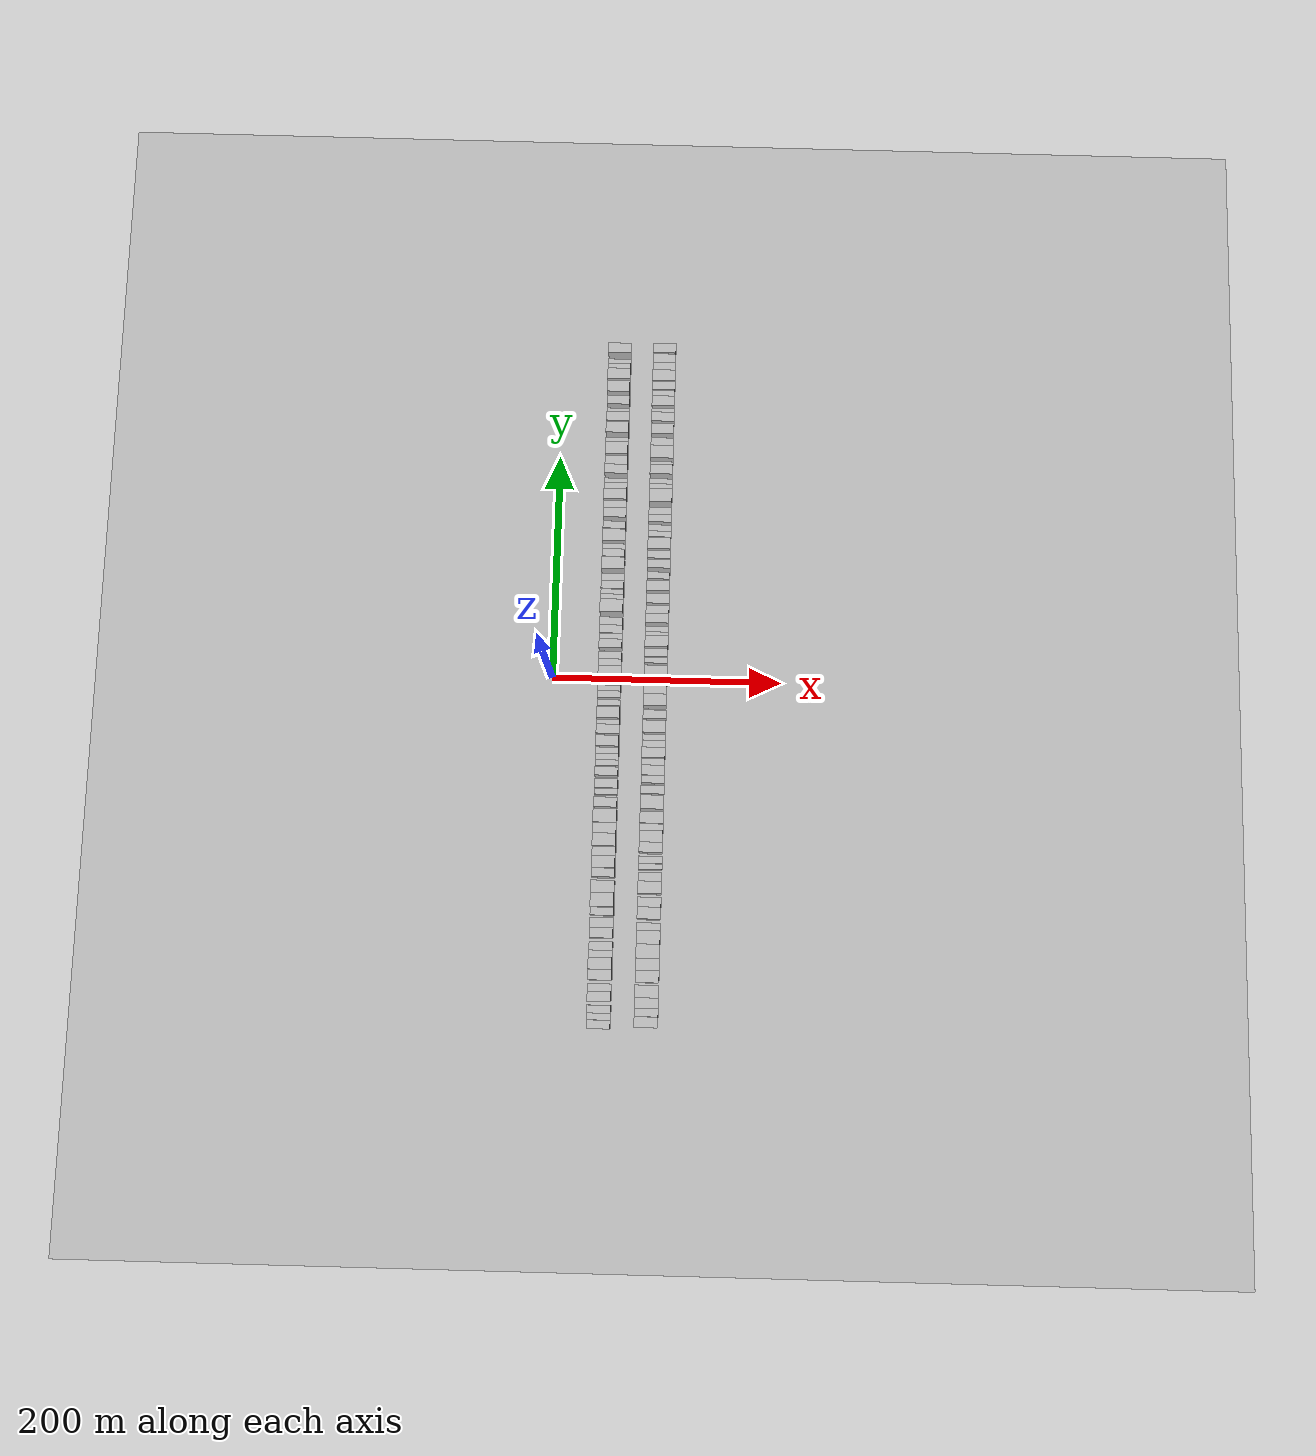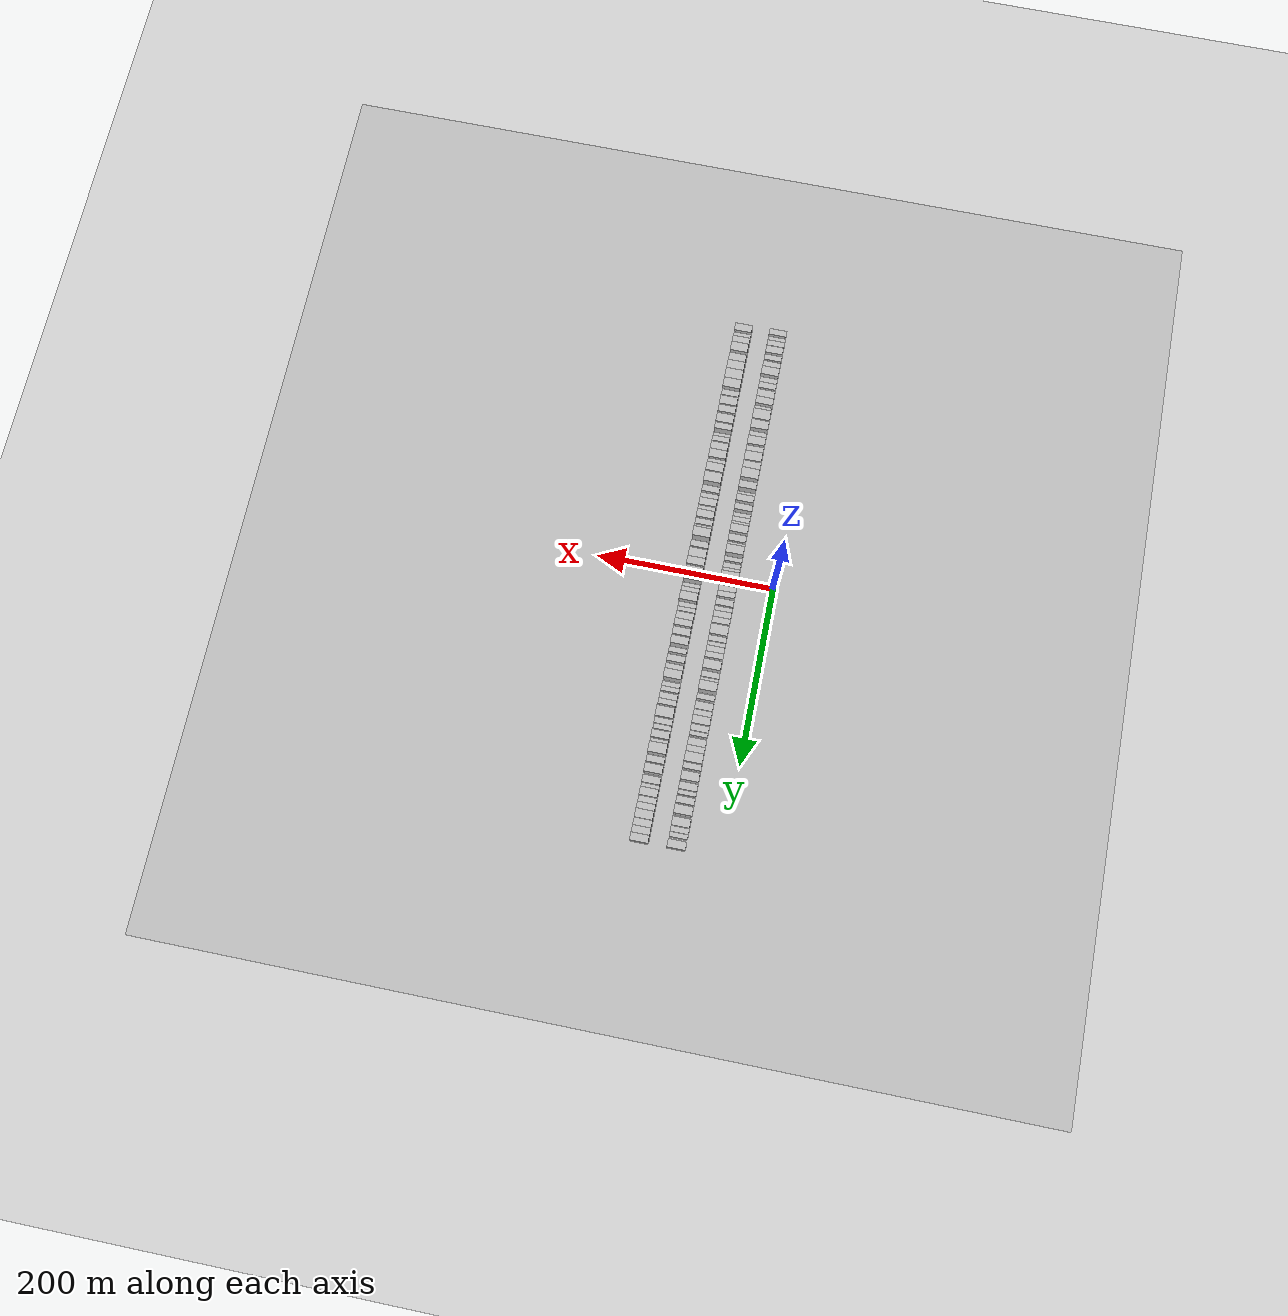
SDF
<?xml version="1.0" encoding="utf-8"?>

<sdf version="1.6">

   <world name="default">

      <gui fullscreen="0">

         <camera name="user_camera">

            <pose>-15 0 4.57585 0 0 0</pose>

            <view_controller>orbit</view_controller>

         </camera>

      </gui>

      <scene>

         <sky>

           <clouds>

             <speed>12</speed>

           </clouds>

         </sky>

         <ambient>0.4 0.4 0.4 1</ambient>

         <background>0.7 0.7 0.7 1</background>

         <shadows>1</shadows>

      </scene>

      <gravity>0 0 -9.8066</gravity>

      <magnetic_field>6e-06 2.3e-05 -4.2e-05</magnetic_field>

      <physics default="0" name="default_physics" type="ode">

         <ode>

            <solver>

               <type>quick</type>

               <iters>10</iters>

               <sor>1.0</sor>

               <use_dynamic_moi_rescaling>0</use_dynamic_moi_rescaling>

            </solver>

            <constraints>

               <cfm>0</cfm>

               <erp>0.2</erp>

               <contact_max_correcting_vel>100</contact_max_correcting_vel>

               <contact_surface_layer>0.001</contact_surface_layer>

            </constraints>

         </ode>

         <max_step_size>0.004</max_step_size>

         <real_time_factor>1</real_time_factor>

         <real_time_update_rate>250</real_time_update_rate>

      </physics>

      <light name="sun" type="directional">

         <cast_shadows>1</cast_shadows>

         <pose>0 0 10 0 0 0</pose>

         <diffuse>0.8 0.8 0.8 1</diffuse>

         <specular>0.2 0.2 0.2 1</specular>

         <attenuation>

            <range>1000</range>

            <constant>0.9</constant>

            <linear>0.01</linear>

            <quadratic>0.001</quadratic>

         </attenuation>

         <direction>-0.5 0.1 -0.9</direction>

      </light>

      <include>

         <name>ground_plane_1</name>

         <uri>model://HANNAS_ground_plane</uri>

         <pose>0 0 0  0 0 0</pose>

      </include>

      <include>

         <name>ground_plane_2</name>

         <uri>model://HANNAS_ground_plane</uri>

         <pose>100 0 0  0 0 0</pose>

      </include>

      <model name="building_1">

         <static>1</static>

         <pose frame="">50.0000 -296.3938 0 0.000000 0.000000 0.000000</pose>

         <link name="link">

            <pose frame="">0 0 9.00 0 0 0</pose>

            <collision name="collision">

               <geometry>

                  <box>

                     <size>20.0000 7.2124 18.0000</size>

                  </box>

               </geometry>

               <max_contacts>10</max_contacts>

               <surface>

                  <contact>

                     <ode/>

                  </contact>

                  <bounce/>

                  <friction>

                     <torsional>

                        <ode/>

                     </torsional>

                     <ode/>

                  </friction>

               </surface>

            </collision>

            <visual name="visual">

               <cast_shadows>0</cast_shadows>

               <geometry>

                  <box>

                     <size>20.0000 7.2124 18.0000</size>

                  </box>

               </geometry>

               <material>

                  <script>

                     <uri>model://HANNAS_wall/materials/scripts</uri>

                     <uri>model://HANNAS_wall/materials/textures</uri>

                     <name>vrc/HANNAS_wall</name>

                  </script>

               </material>

            </visual>

            <self_collide>0</self_collide>

            <enable_wind>0</enable_wind>

            <kinematic>0</kinematic>

         </link>

      </model>

      <model name="building_2">

         <static>1</static>

         <pose frame="">50.0000 -289.9221 0 0.000000 0.000000 0.000000</pose>

         <link name="link">

            <pose frame="">0 0 6.00 0 0 0</pose>

            <collision name="collision">

               <geometry>

                  <box>

                     <size>20.0000 5.7311 12.0000</size>

                  </box>

               </geometry>

               <max_contacts>10</max_contacts>

               <surface>

                  <contact>

                     <ode/>

                  </contact>

                  <bounce/>

                  <friction>

                     <torsional>

                        <ode/>

                     </torsional>

                     <ode/>

                  </friction>

               </surface>

            </collision>

            <visual name="visual">

               <cast_shadows>0</cast_shadows>

               <geometry>

                  <box>

                     <size>20.0000 5.7311 12.0000</size>

                  </box>

               </geometry>

               <material>

                  <script>

                     <uri>model://HANNAS_wall/materials/scripts</uri>

                     <uri>model://HANNAS_wall/materials/textures</uri>

                     <name>vrc/HANNAS_wall</name>

                  </script>

               </material>

            </visual>

            <self_collide>0</self_collide>

            <enable_wind>0</enable_wind>

            <kinematic>0</kinematic>

         </link>

      </model>

      <model name="building_3">

         <static>1</static>

         <pose frame="">50.0000 -283.7980 0 0.000000 0.000000 0.000000</pose>

         <link name="link">

            <pose frame="">0 0 7.50 0 0 0</pose>

            <collision name="collision">

               <geometry>

                  <box>

                     <size>20.0000 6.5171 15.0000</size>

                  </box>

               </geometry>

               <max_contacts>10</max_contacts>

               <surface>

                  <contact>

                     <ode/>

                  </contact>

                  <bounce/>

                  <friction>

                     <torsional>

                        <ode/>

                     </torsional>

                     <ode/>

                  </friction>

               </surface>

            </collision>

            <visual name="visual">

               <cast_shadows>0</cast_shadows>

               <geometry>

                  <box>

                     <size>20.0000 6.5171 15.0000</size>

                  </box>

               </geometry>

               <material>

                  <script>

                     <uri>model://HANNAS_wall/materials/scripts</uri>

                     <uri>model://HANNAS_wall/materials/textures</uri>

                     <name>vrc/HANNAS_wall</name>

                  </script>

               </material>

            </visual>

            <self_collide>0</self_collide>

            <enable_wind>0</enable_wind>

            <kinematic>0</kinematic>

         </link>

      </model>

      <model name="building_4">

         <static>1</static>

         <pose frame="">50.0000 -273.3251 0 0.000000 0.000000 0.000000</pose>

         <link name="link">

            <pose frame="">0 0 10.50 0 0 0</pose>

            <collision name="collision">

               <geometry>

                  <box>

                     <size>20.0000 8.4287 21.0000</size>

                  </box>

               </geometry>

               <max_contacts>10</max_contacts>

               <surface>

                  <contact>

                     <ode/>

                  </contact>

                  <bounce/>

                  <friction>

                     <torsional>

                        <ode/>

                     </torsional>

                     <ode/>

                  </friction>

               </surface>

            </collision>

            <visual name="visual">

               <cast_shadows>0</cast_shadows>

               <geometry>

                  <box>

                     <size>20.0000 8.4287 21.0000</size>

                  </box>

               </geometry>

               <material>

                  <script>

                     <uri>model://HANNAS_wall/materials/scripts</uri>

                     <uri>model://HANNAS_wall/materials/textures</uri>

                     <name>vrc/HANNAS_wall</name>

                  </script>

               </material>

            </visual>

            <self_collide>0</self_collide>

            <enable_wind>0</enable_wind>

            <kinematic>0</kinematic>

         </link>

      </model>

      <model name="building_5">

         <static>1</static>

         <pose frame="">50.0000 -265.8694 0 0.000000 0.000000 0.000000</pose>

         <link name="link">

            <pose frame="">0 0 7.50 0 0 0</pose>

            <collision name="collision">

               <geometry>

                  <box>

                     <size>20.0000 6.4827 15.0000</size>

                  </box>

               </geometry>

               <max_contacts>10</max_contacts>

               <surface>

                  <contact>

                     <ode/>

                  </contact>

                  <bounce/>

                  <friction>

                     <torsional>

                        <ode/>

                     </torsional>

                     <ode/>

                  </friction>

               </surface>

            </collision>

            <visual name="visual">

               <cast_shadows>0</cast_shadows>

               <geometry>

                  <box>

                     <size>20.0000 6.4827 15.0000</size>

                  </box>

               </geometry>

               <material>

                  <script>

                     <uri>model://HANNAS_wall/materials/scripts</uri>

                     <uri>model://HANNAS_wall/materials/textures</uri>

                     <name>vrc/HANNAS_wall</name>

                  </script>

               </material>

            </visual>

            <self_collide>0</self_collide>

            <enable_wind>0</enable_wind>

            <kinematic>0</kinematic>

         </link>

      </model>

      <model name="building_6">

         <static>1</static>

         <pose frame="">50.0000 -255.1822 0 0.000000 0.000000 0.000000</pose>

         <link name="link">

            <pose frame="">0 0 9.00 0 0 0</pose>

            <collision name="collision">

               <geometry>

                  <box>

                     <size>20.0000 8.8916 18.0000</size>

                  </box>

               </geometry>

               <max_contacts>10</max_contacts>

               <surface>

                  <contact>

                     <ode/>

                  </contact>

                  <bounce/>

                  <friction>

                     <torsional>

                        <ode/>

                     </torsional>

                     <ode/>

                  </friction>

               </surface>

            </collision>

            <visual name="visual">

               <cast_shadows>0</cast_shadows>

               <geometry>

                  <box>

                     <size>20.0000 8.8916 18.0000</size>

                  </box>

               </geometry>

               <material>

                  <script>

                     <uri>model://HANNAS_wall/materials/scripts</uri>

                     <uri>model://HANNAS_wall/materials/textures</uri>

                     <name>vrc/HANNAS_wall</name>

                  </script>

               </material>

            </visual>

            <self_collide>0</self_collide>

            <enable_wind>0</enable_wind>

            <kinematic>0</kinematic>

         </link>

      </model>

      <model name="building_7">

         <static>1</static>

         <pose frame="">50.0000 -245.7802 0 0.000000 0.000000 0.000000</pose>

         <link name="link">

            <pose frame="">0 0 12.00 0 0 0</pose>

            <collision name="collision">

               <geometry>

                  <box>

                     <size>20.0000 9.9125 24.0000</size>

                  </box>

               </geometry>

               <max_contacts>10</max_contacts>

               <surface>

                  <contact>

                     <ode/>

                  </contact>

                  <bounce/>

                  <friction>

                     <torsional>

                        <ode/>

                     </torsional>

                     <ode/>

                  </friction>

               </surface>

            </collision>

            <visual name="visual">

               <cast_shadows>0</cast_shadows>

               <geometry>

                  <box>

                     <size>20.0000 9.9125 24.0000</size>

                  </box>

               </geometry>

               <material>

                  <script>

                     <uri>model://HANNAS_wall/materials/scripts</uri>

                     <uri>model://HANNAS_wall/materials/textures</uri>

                     <name>vrc/HANNAS_wall</name>

                  </script>

               </material>

            </visual>

            <self_collide>0</self_collide>

            <enable_wind>0</enable_wind>

            <kinematic>0</kinematic>

         </link>

      </model>

      <model name="building_8">

         <static>1</static>

         <pose frame="">50.0000 -237.7460 0 0.000000 0.000000 0.000000</pose>

         <link name="link">

            <pose frame="">0 0 7.50 0 0 0</pose>

            <collision name="collision">

               <geometry>

                  <box>

                     <size>20.0000 6.1559 15.0000</size>

                  </box>

               </geometry>

               <max_contacts>10</max_contacts>

               <surface>

                  <contact>

                     <ode/>

                  </contact>

                  <bounce/>

                  <friction>

                     <torsional>

                        <ode/>

                     </torsional>

                     <ode/>

                  </friction>

               </surface>

            </collision>

            <visual name="visual">

               <cast_shadows>0</cast_shadows>

               <geometry>

                  <box>

                     <size>20.0000 6.1559 15.0000</size>

                  </box>

               </geometry>

               <material>

                  <script>

                     <uri>model://HANNAS_wall/materials/scripts</uri>

                     <uri>model://HANNAS_wall/materials/textures</uri>

                     <name>vrc/HANNAS_wall</name>

                  </script>

               </material>

            </visual>

            <self_collide>0</self_collide>

            <enable_wind>0</enable_wind>

            <kinematic>0</kinematic>

         </link>

      </model>

      <model name="building_9">

         <static>1</static>

         <pose frame="">50.0000 -231.0700 0 0.000000 0.000000 0.000000</pose>

         <link name="link">

            <pose frame="">0 0 7.50 0 0 0</pose>

            <collision name="collision">

               <geometry>

                  <box>

                     <size>20.0000 7.1961 15.0000</size>

                  </box>

               </geometry>

               <max_contacts>10</max_contacts>

               <surface>

                  <contact>

                     <ode/>

                  </contact>

                  <bounce/>

                  <friction>

                     <torsional>

                        <ode/>

                     </torsional>

                     <ode/>

                  </friction>

               </surface>

            </collision>

            <visual name="visual">

               <cast_shadows>0</cast_shadows>

               <geometry>

                  <box>

                     <size>20.0000 7.1961 15.0000</size>

                  </box>

               </geometry>

               <material>

                  <script>

                     <uri>model://HANNAS_wall/materials/scripts</uri>

                     <uri>model://HANNAS_wall/materials/textures</uri>

                     <name>vrc/HANNAS_wall</name>

                  </script>

               </material>

            </visual>

            <self_collide>0</self_collide>

            <enable_wind>0</enable_wind>

            <kinematic>0</kinematic>

         </link>

      </model>

      <model name="building_10">

         <static>1</static>

         <pose frame="">50.0000 -220.1311 0 0.000000 0.000000 0.000000</pose>

         <link name="link">

            <pose frame="">0 0 9.00 0 0 0</pose>

            <collision name="collision">

               <geometry>

                  <box>

                     <size>20.0000 8.6818 18.0000</size>

                  </box>

               </geometry>

               <max_contacts>10</max_contacts>

               <surface>

                  <contact>

                     <ode/>

                  </contact>

                  <bounce/>

                  <friction>

                     <torsional>

                        <ode/>

                     </torsional>

                     <ode/>

                  </friction>

               </surface>

            </collision>

            <visual name="visual">

               <cast_shadows>0</cast_shadows>

               <geometry>

                  <box>

                     <size>20.0000 8.6818 18.0000</size>

                  </box>

               </geometry>

               <material>

                  <script>

                     <uri>model://HANNAS_wall/materials/scripts</uri>

                     <uri>model://HANNAS_wall/materials/textures</uri>

                     <name>vrc/HANNAS_wall</name>

                  </script>

               </material>

            </visual>

            <self_collide>0</self_collide>

            <enable_wind>0</enable_wind>

            <kinematic>0</kinematic>

         </link>

      </model>

      <model name="building_11">

         <static>1</static>

         <pose frame="">50.0000 -211.5298 0 0.000000 0.000000 0.000000</pose>

         <link name="link">

            <pose frame="">0 0 9.00 0 0 0</pose>

            <collision name="collision">

               <geometry>

                  <box>

                     <size>20.0000 8.5208 18.0000</size>

                  </box>

               </geometry>

               <max_contacts>10</max_contacts>

               <surface>

                  <contact>

                     <ode/>

                  </contact>

                  <bounce/>

                  <friction>

                     <torsional>

                        <ode/>

                     </torsional>

                     <ode/>

                  </friction>

               </surface>

            </collision>

            <visual name="visual">

               <cast_shadows>0</cast_shadows>

               <geometry>

                  <box>

                     <size>20.0000 8.5208 18.0000</size>

                  </box>

               </geometry>

               <material>

                  <script>

                     <uri>model://HANNAS_wall/materials/scripts</uri>

                     <uri>model://HANNAS_wall/materials/textures</uri>

                     <name>vrc/HANNAS_wall</name>

                  </script>

               </material>

            </visual>

            <self_collide>0</self_collide>

            <enable_wind>0</enable_wind>

            <kinematic>0</kinematic>

         </link>

      </model>

      <model name="building_12">

         <static>1</static>

         <pose frame="">50.0000 -201.8621 0 0.000000 0.000000 0.000000</pose>

         <link name="link">

            <pose frame="">0 0 7.50 0 0 0</pose>

            <collision name="collision">

               <geometry>

                  <box>

                     <size>20.0000 6.8145 15.0000</size>

                  </box>

               </geometry>

               <max_contacts>10</max_contacts>

               <surface>

                  <contact>

                     <ode/>

                  </contact>

                  <bounce/>

                  <friction>

                     <torsional>

                        <ode/>

                     </torsional>

                     <ode/>

                  </friction>

               </surface>

            </collision>

            <visual name="visual">

               <cast_shadows>0</cast_shadows>

               <geometry>

                  <box>

                     <size>20.0000 6.8145 15.0000</size>

                  </box>

               </geometry>

               <material>

                  <script>

                     <uri>model://HANNAS_wall/materials/scripts</uri>

                     <uri>model://HANNAS_wall/materials/textures</uri>

                     <name>vrc/HANNAS_wall</name>

                  </script>

               </material>

            </visual>

            <self_collide>0</self_collide>

            <enable_wind>0</enable_wind>

            <kinematic>0</kinematic>

         </link>

      </model>

      <model name="building_13">

         <static>1</static>

         <pose frame="">50.0000 -192.4567 0 0.000000 0.000000 0.000000</pose>

         <link name="link">

            <pose frame="">0 0 12.00 0 0 0</pose>

            <collision name="collision">

               <geometry>

                  <box>

                     <size>20.0000 11.9965 24.0000</size>

                  </box>

               </geometry>

               <max_contacts>10</max_contacts>

               <surface>

                  <contact>

                     <ode/>

                  </contact>

                  <bounce/>

                  <friction>

                     <torsional>

                        <ode/>

                     </torsional>

                     <ode/>

                  </friction>

               </surface>

            </collision>

            <visual name="visual">

               <cast_shadows>0</cast_shadows>

               <geometry>

                  <box>

                     <size>20.0000 11.9965 24.0000</size>

                  </box>

               </geometry>

               <material>

                  <script>

                     <uri>model://HANNAS_wall/materials/scripts</uri>

                     <uri>model://HANNAS_wall/materials/textures</uri>

                     <name>vrc/HANNAS_wall</name>

                  </script>

               </material>

            </visual>

            <self_collide>0</self_collide>

            <enable_wind>0</enable_wind>

            <kinematic>0</kinematic>

         </link>

      </model>

      <model name="building_14">

         <static>1</static>

         <pose frame="">50.0000 -181.2422 0 0.000000 0.000000 0.000000</pose>

         <link name="link">

            <pose frame="">0 0 10.50 0 0 0</pose>

            <collision name="collision">

               <geometry>

                  <box>

                     <size>20.0000 10.4326 21.0000</size>

                  </box>

               </geometry>

               <max_contacts>10</max_contacts>

               <surface>

                  <contact>

                     <ode/>

                  </contact>

                  <bounce/>

                  <friction>

                     <torsional>

                        <ode/>

                     </torsional>

                     <ode/>

                  </friction>

               </surface>

            </collision>

            <visual name="visual">

               <cast_shadows>0</cast_shadows>

               <geometry>

                  <box>

                     <size>20.0000 10.4326 21.0000</size>

                  </box>

               </geometry>

               <material>

                  <script>

                     <uri>model://HANNAS_wall/materials/scripts</uri>

                     <uri>model://HANNAS_wall/materials/textures</uri>

                     <name>vrc/HANNAS_wall</name>

                  </script>

               </material>

            </visual>

            <self_collide>0</self_collide>

            <enable_wind>0</enable_wind>

            <kinematic>0</kinematic>

         </link>

      </model>

      <model name="building_15">

         <static>1</static>

         <pose frame="">50.0000 -169.2734 0 0.000000 0.000000 0.000000</pose>

         <link name="link">

            <pose frame="">0 0 9.00 0 0 0</pose>

            <collision name="collision">

               <geometry>

                  <box>

                     <size>20.0000 7.5050 18.0000</size>

                  </box>

               </geometry>

               <max_contacts>10</max_contacts>

               <surface>

                  <contact>

                     <ode/>

                  </contact>

                  <bounce/>

                  <friction>

                     <torsional>

                        <ode/>

                     </torsional>

                     <ode/>

                  </friction>

               </surface>

            </collision>

            <visual name="visual">

               <cast_shadows>0</cast_shadows>

               <geometry>

                  <box>

                     <size>20.0000 7.5050 18.0000</size>

                  </box>

               </geometry>

               <material>

                  <script>

                     <uri>model://HANNAS_wall/materials/scripts</uri>

                     <uri>model://HANNAS_wall/materials/textures</uri>

                     <name>vrc/HANNAS_wall</name>

                  </script>

               </material>

            </visual>

            <self_collide>0</self_collide>

            <enable_wind>0</enable_wind>

            <kinematic>0</kinematic>

         </link>

      </model>

      <model name="building_16">

         <static>1</static>

         <pose frame="">50.0000 -160.4951 0 0.000000 0.000000 0.000000</pose>

         <link name="link">

            <pose frame="">0 0 12.00 0 0 0</pose>

            <collision name="collision">

               <geometry>

                  <box>

                     <size>20.0000 10.0514 24.0000</size>

                  </box>

               </geometry>

               <max_contacts>10</max_contacts>

               <surface>

                  <contact>

                     <ode/>

                  </contact>

                  <bounce/>

                  <friction>

                     <torsional>

                        <ode/>

                     </torsional>

                     <ode/>

                  </friction>

               </surface>

            </collision>

            <visual name="visual">

               <cast_shadows>0</cast_shadows>

               <geometry>

                  <box>

                     <size>20.0000 10.0514 24.0000</size>

                  </box>

               </geometry>

               <material>

                  <script>

                     <uri>model://HANNAS_wall/materials/scripts</uri>

                     <uri>model://HANNAS_wall/materials/textures</uri>

                     <name>vrc/HANNAS_wall</name>

                  </script>

               </material>

            </visual>

            <self_collide>0</self_collide>

            <enable_wind>0</enable_wind>

            <kinematic>0</kinematic>

         </link>

      </model>

      <model name="building_17">

         <static>1</static>

         <pose frame="">50.0000 -151.2914 0 0.000000 0.000000 0.000000</pose>

         <link name="link">

            <pose frame="">0 0 9.00 0 0 0</pose>

            <collision name="collision">

               <geometry>

                  <box>

                     <size>20.0000 8.3562 18.0000</size>

                  </box>

               </geometry>

               <max_contacts>10</max_contacts>

               <surface>

                  <contact>

                     <ode/>

                  </contact>

                  <bounce/>

                  <friction>

                     <torsional>

                        <ode/>

                     </torsional>

                     <ode/>

                  </friction>

               </surface>

            </collision>

            <visual name="visual">

               <cast_shadows>0</cast_shadows>

               <geometry>

                  <box>

                     <size>20.0000 8.3562 18.0000</size>

                  </box>

               </geometry>

               <material>

                  <script>

                     <uri>model://HANNAS_wall/materials/scripts</uri>

                     <uri>model://HANNAS_wall/materials/textures</uri>

                     <name>vrc/HANNAS_wall</name>

                  </script>

               </material>

            </visual>

            <self_collide>0</self_collide>

            <enable_wind>0</enable_wind>

            <kinematic>0</kinematic>

         </link>

      </model>

      <model name="building_18">

         <static>1</static>

         <pose frame="">50.0000 -141.6628 0 0.000000 0.000000 0.000000</pose>

         <link name="link">

            <pose frame="">0 0 12.00 0 0 0</pose>

            <collision name="collision">

               <geometry>

                  <box>

                     <size>20.0000 10.9010 24.0000</size>

                  </box>

               </geometry>

               <max_contacts>10</max_contacts>

               <surface>

                  <contact>

                     <ode/>

                  </contact>

                  <bounce/>

                  <friction>

                     <torsional>

                        <ode/>

                     </torsional>

                     <ode/>

                  </friction>

               </surface>

            </collision>

            <visual name="visual">

               <cast_shadows>0</cast_shadows>

               <geometry>

                  <box>

                     <size>20.0000 10.9010 24.0000</size>

                  </box>

               </geometry>

               <material>

                  <script>

                     <uri>model://HANNAS_wall/materials/scripts</uri>

                     <uri>model://HANNAS_wall/materials/textures</uri>

                     <name>vrc/HANNAS_wall</name>

                  </script>

               </material>

            </visual>

            <self_collide>0</self_collide>

            <enable_wind>0</enable_wind>

            <kinematic>0</kinematic>

         </link>

      </model>

      <model name="building_19">

         <static>1</static>

         <pose frame="">50.0000 -131.6414 0 0.000000 0.000000 0.000000</pose>

         <link name="link">

            <pose frame="">0 0 10.50 0 0 0</pose>

            <collision name="collision">

               <geometry>

                  <box>

                     <size>20.0000 9.1419 21.0000</size>

                  </box>

               </geometry>

               <max_contacts>10</max_contacts>

               <surface>

                  <contact>

                     <ode/>

                  </contact>

                  <bounce/>

                  <friction>

                     <torsional>

                        <ode/>

                     </torsional>

                     <ode/>

                  </friction>

               </surface>

            </collision>

            <visual name="visual">

               <cast_shadows>0</cast_shadows>

               <geometry>

                  <box>

                     <size>20.0000 9.1419 21.0000</size>

                  </box>

               </geometry>

               <material>

                  <script>

                     <uri>model://HANNAS_wall/materials/scripts</uri>

                     <uri>model://HANNAS_wall/materials/textures</uri>

                     <name>vrc/HANNAS_wall</name>

                  </script>

               </material>

            </visual>

            <self_collide>0</self_collide>

            <enable_wind>0</enable_wind>

            <kinematic>0</kinematic>

         </link>

      </model>

      <model name="building_20">

         <static>1</static>

         <pose frame="">50.0000 -121.2300 0 0.000000 0.000000 0.000000</pose>

         <link name="link">

            <pose frame="">0 0 12.00 0 0 0</pose>

            <collision name="collision">

               <geometry>

                  <box>

                     <size>20.0000 11.6808 24.0000</size>

                  </box>

               </geometry>

               <max_contacts>10</max_contacts>

               <surface>

                  <contact>

                     <ode/>

                  </contact>

                  <bounce/>

                  <friction>

                     <torsional>

                        <ode/>

                     </torsional>

                     <ode/>

                  </friction>

               </surface>

            </collision>

            <visual name="visual">

               <cast_shadows>0</cast_shadows>

               <geometry>

                  <box>

                     <size>20.0000 11.6808 24.0000</size>

                  </box>

               </geometry>

               <material>

                  <script>

                     <uri>model://HANNAS_wall/materials/scripts</uri>

                     <uri>model://HANNAS_wall/materials/textures</uri>

                     <name>vrc/HANNAS_wall</name>

                  </script>

               </material>

            </visual>

            <self_collide>0</self_collide>

            <enable_wind>0</enable_wind>

            <kinematic>0</kinematic>

         </link>

      </model>

      <model name="building_21">

         <static>1</static>

         <pose frame="">50.0000 -109.1669 0 0.000000 0.000000 0.000000</pose>

         <link name="link">

            <pose frame="">0 0 9.00 0 0 0</pose>

            <collision name="collision">

               <geometry>

                  <box>

                     <size>20.0000 8.4455 18.0000</size>

                  </box>

               </geometry>

               <max_contacts>10</max_contacts>

               <surface>

                  <contact>

                     <ode/>

                  </contact>

                  <bounce/>

                  <friction>

                     <torsional>

                        <ode/>

                     </torsional>

                     <ode/>

                  </friction>

               </surface>

            </collision>

            <visual name="visual">

               <cast_shadows>0</cast_shadows>

               <geometry>

                  <box>

                     <size>20.0000 8.4455 18.0000</size>

                  </box>

               </geometry>

               <material>

                  <script>

                     <uri>model://HANNAS_wall/materials/scripts</uri>

                     <uri>model://HANNAS_wall/materials/textures</uri>

                     <name>vrc/HANNAS_wall</name>

                  </script>

               </material>

            </visual>

            <self_collide>0</self_collide>

            <enable_wind>0</enable_wind>

            <kinematic>0</kinematic>

         </link>

      </model>

      <model name="building_22">

         <static>1</static>

         <pose frame="">50.0000 -99.4959 0 0.000000 0.000000 0.000000</pose>

         <link name="link">

            <pose frame="">0 0 6.00 0 0 0</pose>

            <collision name="collision">

               <geometry>

                  <box>

                     <size>20.0000 4.8965 12.0000</size>

                  </box>

               </geometry>

               <max_contacts>10</max_contacts>

               <surface>

                  <contact>

                     <ode/>

                  </contact>

                  <bounce/>

                  <friction>

                     <torsional>

                        <ode/>

                     </torsional>

                     <ode/>

                  </friction>

               </surface>

            </collision>

            <visual name="visual">

               <cast_shadows>0</cast_shadows>

               <geometry>

                  <box>

                     <size>20.0000 4.8965 12.0000</size>

                  </box>

               </geometry>

               <material>

                  <script>

                     <uri>model://HANNAS_wall/materials/scripts</uri>

                     <uri>model://HANNAS_wall/materials/textures</uri>

                     <name>vrc/HANNAS_wall</name>

                  </script>

               </material>

            </visual>

            <self_collide>0</self_collide>

            <enable_wind>0</enable_wind>

            <kinematic>0</kinematic>

         </link>

      </model>

      <model name="building_23">

         <static>1</static>

         <pose frame="">50.0000 -93.1157 0 0.000000 0.000000 0.000000</pose>

         <link name="link">

            <pose frame="">0 0 9.00 0 0 0</pose>

            <collision name="collision">

               <geometry>

                  <box>

                     <size>20.0000 7.8640 18.0000</size>

                  </box>

               </geometry>

               <max_contacts>10</max_contacts>

               <surface>

                  <contact>

                     <ode/>

                  </contact>

                  <bounce/>

                  <friction>

                     <torsional>

                        <ode/>

                     </torsional>

                     <ode/>

                  </friction>

               </surface>

            </collision>

            <visual name="visual">

               <cast_shadows>0</cast_shadows>

               <geometry>

                  <box>

                     <size>20.0000 7.8640 18.0000</size>

                  </box>

               </geometry>

               <material>

                  <script>

                     <uri>model://HANNAS_wall/materials/scripts</uri>

                     <uri>model://HANNAS_wall/materials/textures</uri>

                     <name>vrc/HANNAS_wall</name>

                  </script>

               </material>

            </visual>

            <self_collide>0</self_collide>

            <enable_wind>0</enable_wind>

            <kinematic>0</kinematic>

         </link>

      </model>

      <model name="building_24">

         <static>1</static>

         <pose frame="">50.0000 -82.5297 0 0.000000 0.000000 0.000000</pose>

         <link name="link">

            <pose frame="">0 0 9.00 0 0 0</pose>

            <collision name="collision">

               <geometry>

                  <box>

                     <size>20.0000 7.3079 18.0000</size>

                  </box>

               </geometry>

               <max_contacts>10</max_contacts>

               <surface>

                  <contact>

                     <ode/>

                  </contact>

                  <bounce/>

                  <friction>

                     <torsional>

                        <ode/>

                     </torsional>

                     <ode/>

                  </friction>

               </surface>

            </collision>

            <visual name="visual">

               <cast_shadows>0</cast_shadows>

               <geometry>

                  <box>

                     <size>20.0000 7.3079 18.0000</size>

                  </box>

               </geometry>

               <material>

                  <script>

                     <uri>model://HANNAS_wall/materials/scripts</uri>

                     <uri>model://HANNAS_wall/materials/textures</uri>

                     <name>vrc/HANNAS_wall</name>

                  </script>

               </material>

            </visual>

            <self_collide>0</self_collide>

            <enable_wind>0</enable_wind>

            <kinematic>0</kinematic>

         </link>

      </model>

      <model name="building_25">

         <static>1</static>

         <pose frame="">50.0000 -74.4745 0 0.000000 0.000000 0.000000</pose>

         <link name="link">

            <pose frame="">0 0 6.00 0 0 0</pose>

            <collision name="collision">

               <geometry>

                  <box>

                     <size>20.0000 4.8025 12.0000</size>

                  </box>

               </geometry>

               <max_contacts>10</max_contacts>

               <surface>

                  <contact>

                     <ode/>

                  </contact>

                  <bounce/>

                  <friction>

                     <torsional>

                        <ode/>

                     </torsional>

                     <ode/>

                  </friction>

               </surface>

            </collision>

            <visual name="visual">

               <cast_shadows>0</cast_shadows>

               <geometry>

                  <box>

                     <size>20.0000 4.8025 12.0000</size>

                  </box>

               </geometry>

               <material>

                  <script>

                     <uri>model://HANNAS_wall/materials/scripts</uri>

                     <uri>model://HANNAS_wall/materials/textures</uri>

                     <name>vrc/HANNAS_wall</name>

                  </script>

               </material>

            </visual>

            <self_collide>0</self_collide>

            <enable_wind>0</enable_wind>

            <kinematic>0</kinematic>

         </link>

      </model>

      <model name="building_26">

         <static>1</static>

         <pose frame="">50.0000 -69.2861 0 0.000000 0.000000 0.000000</pose>

         <link name="link">

            <pose frame="">0 0 6.00 0 0 0</pose>

            <collision name="collision">

               <geometry>

                  <box>

                     <size>20.0000 5.5743 12.0000</size>

                  </box>

               </geometry>

               <max_contacts>10</max_contacts>

               <surface>

                  <contact>

                     <ode/>

                  </contact>

                  <bounce/>

                  <friction>

                     <torsional>

                        <ode/>

                     </torsional>

                     <ode/>

                  </friction>

               </surface>

            </collision>

            <visual name="visual">

               <cast_shadows>0</cast_shadows>

               <geometry>

                  <box>

                     <size>20.0000 5.5743 12.0000</size>

                  </box>

               </geometry>

               <material>

                  <script>

                     <uri>model://HANNAS_wall/materials/scripts</uri>

                     <uri>model://HANNAS_wall/materials/textures</uri>

                     <name>vrc/HANNAS_wall</name>

                  </script>

               </material>

            </visual>

            <self_collide>0</self_collide>

            <enable_wind>0</enable_wind>

            <kinematic>0</kinematic>

         </link>

      </model>

      <model name="building_27">

         <static>1</static>

         <pose frame="">50.0000 -63.8229 0 0.000000 0.000000 0.000000</pose>

         <link name="link">

            <pose frame="">0 0 6.00 0 0 0</pose>

            <collision name="collision">

               <geometry>

                  <box>

                     <size>20.0000 5.3521 12.0000</size>

                  </box>

               </geometry>

               <max_contacts>10</max_contacts>

               <surface>

                  <contact>

                     <ode/>

                  </contact>

                  <bounce/>

                  <friction>

                     <torsional>

                        <ode/>

                     </torsional>

                     <ode/>

                  </friction>

               </surface>

            </collision>

            <visual name="visual">

               <cast_shadows>0</cast_shadows>

               <geometry>

                  <box>

                     <size>20.0000 5.3521 12.0000</size>

                  </box>

               </geometry>

               <material>

                  <script>

                     <uri>model://HANNAS_wall/materials/scripts</uri>

                     <uri>model://HANNAS_wall/materials/textures</uri>

                     <name>vrc/HANNAS_wall</name>

                  </script>

               </material>

            </visual>

            <self_collide>0</self_collide>

            <enable_wind>0</enable_wind>

            <kinematic>0</kinematic>

         </link>

      </model>

      <model name="building_28">

         <static>1</static>

         <pose frame="">50.0000 -56.4965 0 0.000000 0.000000 0.000000</pose>

         <link name="link">

            <pose frame="">0 0 10.50 0 0 0</pose>

            <collision name="collision">

               <geometry>

                  <box>

                     <size>20.0000 9.3006 21.0000</size>

                  </box>

               </geometry>

               <max_contacts>10</max_contacts>

               <surface>

                  <contact>

                     <ode/>

                  </contact>

                  <bounce/>

                  <friction>

                     <torsional>

                        <ode/>

                     </torsional>

                     <ode/>

                  </friction>

               </surface>

            </collision>

            <visual name="visual">

               <cast_shadows>0</cast_shadows>

               <geometry>

                  <box>

                     <size>20.0000 9.3006 21.0000</size>

                  </box>

               </geometry>

               <material>

                  <script>

                     <uri>model://HANNAS_wall/materials/scripts</uri>

                     <uri>model://HANNAS_wall/materials/textures</uri>

                     <name>vrc/HANNAS_wall</name>

                  </script>

               </material>

            </visual>

            <self_collide>0</self_collide>

            <enable_wind>0</enable_wind>

            <kinematic>0</kinematic>

         </link>

      </model>

      <model name="building_29">

         <static>1</static>

         <pose frame="">50.0000 -45.8440 0 0.000000 0.000000 0.000000</pose>

         <link name="link">

            <pose frame="">0 0 9.00 0 0 0</pose>

            <collision name="collision">

               <geometry>

                  <box>

                     <size>20.0000 8.0045 18.0000</size>

                  </box>

               </geometry>

               <max_contacts>10</max_contacts>

               <surface>

                  <contact>

                     <ode/>

                  </contact>

                  <bounce/>

                  <friction>

                     <torsional>

                        <ode/>

                     </torsional>

                     <ode/>

                  </friction>

               </surface>

            </collision>

            <visual name="visual">

               <cast_shadows>0</cast_shadows>

               <geometry>

                  <box>

                     <size>20.0000 8.0045 18.0000</size>

                  </box>

               </geometry>

               <material>

                  <script>

                     <uri>model://HANNAS_wall/materials/scripts</uri>

                     <uri>model://HANNAS_wall/materials/textures</uri>

                     <name>vrc/HANNAS_wall</name>

                  </script>

               </material>

            </visual>

            <self_collide>0</self_collide>

            <enable_wind>0</enable_wind>

            <kinematic>0</kinematic>

         </link>

      </model>

      <model name="building_30">

         <static>1</static>

         <pose frame="">50.0000 -39.3203 0 0.000000 0.000000 0.000000</pose>

         <link name="link">

            <pose frame="">0 0 6.00 0 0 0</pose>

            <collision name="collision">

               <geometry>

                  <box>

                     <size>20.0000 5.0430 12.0000</size>

                  </box>

               </geometry>

               <max_contacts>10</max_contacts>

               <surface>

                  <contact>

                     <ode/>

                  </contact>

                  <bounce/>

                  <friction>

                     <torsional>

                        <ode/>

                     </torsional>

                     <ode/>

                  </friction>

               </surface>

            </collision>

            <visual name="visual">

               <cast_shadows>0</cast_shadows>

               <geometry>

                  <box>

                     <size>20.0000 5.0430 12.0000</size>

                  </box>

               </geometry>

               <material>

                  <script>

                     <uri>model://HANNAS_wall/materials/scripts</uri>

                     <uri>model://HANNAS_wall/materials/textures</uri>

                     <name>vrc/HANNAS_wall</name>

                  </script>

               </material>

            </visual>

            <self_collide>0</self_collide>

            <enable_wind>0</enable_wind>

            <kinematic>0</kinematic>

         </link>

      </model>

      <model name="building_31">

         <static>1</static>

         <pose frame="">50.0000 -31.8423 0 0.000000 0.000000 0.000000</pose>

         <link name="link">

            <pose frame="">0 0 10.50 0 0 0</pose>

            <collision name="collision">

               <geometry>

                  <box>

                     <size>20.0000 9.9128 21.0000</size>

                  </box>

               </geometry>

               <max_contacts>10</max_contacts>

               <surface>

                  <contact>

                     <ode/>

                  </contact>

                  <bounce/>

                  <friction>

                     <torsional>

                        <ode/>

                     </torsional>

                     <ode/>

                  </friction>

               </surface>

            </collision>

            <visual name="visual">

               <cast_shadows>0</cast_shadows>

               <geometry>

                  <box>

                     <size>20.0000 9.9128 21.0000</size>

                  </box>

               </geometry>

               <material>

                  <script>

                     <uri>model://HANNAS_wall/materials/scripts</uri>

                     <uri>model://HANNAS_wall/materials/textures</uri>

                     <name>vrc/HANNAS_wall</name>

                  </script>

               </material>

            </visual>

            <self_collide>0</self_collide>

            <enable_wind>0</enable_wind>

            <kinematic>0</kinematic>

         </link>

      </model>

      <model name="building_32">

         <static>1</static>

         <pose frame="">50.0000 -22.2668 0 0.000000 0.000000 0.000000</pose>

         <link name="link">

            <pose frame="">0 0 6.00 0 0 0</pose>

            <collision name="collision">

               <geometry>

                  <box>

                     <size>20.0000 5.2384 12.0000</size>

                  </box>

               </geometry>

               <max_contacts>10</max_contacts>

               <surface>

                  <contact>

                     <ode/>

                  </contact>

                  <bounce/>

                  <friction>

                     <torsional>

                        <ode/>

                     </torsional>

                     <ode/>

                  </friction>

               </surface>

            </collision>

            <visual name="visual">

               <cast_shadows>0</cast_shadows>

               <geometry>

                  <box>

                     <size>20.0000 5.2384 12.0000</size>

                  </box>

               </geometry>

               <material>

                  <script>

                     <uri>model://HANNAS_wall/materials/scripts</uri>

                     <uri>model://HANNAS_wall/materials/textures</uri>

                     <name>vrc/HANNAS_wall</name>

                  </script>

               </material>

            </visual>

            <self_collide>0</self_collide>

            <enable_wind>0</enable_wind>

            <kinematic>0</kinematic>

         </link>

      </model>

      <model name="building_33">

         <static>1</static>

         <pose frame="">50.0000 -14.6996 0 0.000000 0.000000 0.000000</pose>

         <link name="link">

            <pose frame="">0 0 6.00 0 0 0</pose>

            <collision name="collision">

               <geometry>

                  <box>

                     <size>20.0000 5.8960 12.0000</size>

                  </box>

               </geometry>

               <max_contacts>10</max_contacts>

               <surface>

                  <contact>

                     <ode/>

                  </contact>

                  <bounce/>

                  <friction>

                     <torsional>

                        <ode/>

                     </torsional>

                     <ode/>

                  </friction>

               </surface>

            </collision>

            <visual name="visual">

               <cast_shadows>0</cast_shadows>

               <geometry>

                  <box>

                     <size>20.0000 5.8960 12.0000</size>

                  </box>

               </geometry>

               <material>

                  <script>

                     <uri>model://HANNAS_wall/materials/scripts</uri>

                     <uri>model://HANNAS_wall/materials/textures</uri>

                     <name>vrc/HANNAS_wall</name>

                  </script>

               </material>

            </visual>

            <self_collide>0</self_collide>

            <enable_wind>0</enable_wind>

            <kinematic>0</kinematic>

         </link>

      </model>

      <model name="building_34">

         <static>1</static>

         <pose frame="">50.0000 -9.2656 0 0.000000 0.000000 0.000000</pose>

         <link name="link">

            <pose frame="">0 0 6.00 0 0 0</pose>

            <collision name="collision">

               <geometry>

                  <box>

                     <size>20.0000 4.9720 12.0000</size>

                  </box>

               </geometry>

               <max_contacts>10</max_contacts>

               <surface>

                  <contact>

                     <ode/>

                  </contact>

                  <bounce/>

                  <friction>

                     <torsional>

                        <ode/>

                     </torsional>

                     <ode/>

                  </friction>

               </surface>

            </collision>

            <visual name="visual">

               <cast_shadows>0</cast_shadows>

               <geometry>

                  <box>

                     <size>20.0000 4.9720 12.0000</size>

                  </box>

               </geometry>

               <material>

                  <script>

                     <uri>model://HANNAS_wall/materials/scripts</uri>

                     <uri>model://HANNAS_wall/materials/textures</uri>

                     <name>vrc/HANNAS_wall</name>

                  </script>

               </material>

            </visual>

            <self_collide>0</self_collide>

            <enable_wind>0</enable_wind>

            <kinematic>0</kinematic>

         </link>

      </model>

      <model name="building_35">

         <static>1</static>

         <pose frame="">50.0000 -2.9061 0 0.000000 0.000000 0.000000</pose>

         <link name="link">

            <pose frame="">0 0 9.00 0 0 0</pose>

            <collision name="collision">

               <geometry>

                  <box>

                     <size>20.0000 7.7469 18.0000</size>

                  </box>

               </geometry>

               <max_contacts>10</max_contacts>

               <surface>

                  <contact>

                     <ode/>

                  </contact>

                  <bounce/>

                  <friction>

                     <torsional>

                        <ode/>

                     </torsional>

                     <ode/>

                  </friction>

               </surface>

            </collision>

            <visual name="visual">

               <cast_shadows>0</cast_shadows>

               <geometry>

                  <box>

                     <size>20.0000 7.7469 18.0000</size>

                  </box>

               </geometry>

               <material>

                  <script>

                     <uri>model://HANNAS_wall/materials/scripts</uri>

                     <uri>model://HANNAS_wall/materials/textures</uri>

                     <name>vrc/HANNAS_wall</name>

                  </script>

               </material>

            </visual>

            <self_collide>0</self_collide>

            <enable_wind>0</enable_wind>

            <kinematic>0</kinematic>

         </link>

      </model>

      <model name="building_36">

         <static>1</static>

         <pose frame="">50.0000 5.1324 0 0.000000 0.000000 0.000000</pose>

         <link name="link">

            <pose frame="">0 0 9.00 0 0 0</pose>

            <collision name="collision">

               <geometry>

                  <box>

                     <size>20.0000 8.3301 18.0000</size>

                  </box>

               </geometry>

               <max_contacts>10</max_contacts>

               <surface>

                  <contact>

                     <ode/>

                  </contact>

                  <bounce/>

                  <friction>

                     <torsional>

                        <ode/>

                     </torsional>

                     <ode/>

                  </friction>

               </surface>

            </collision>

            <visual name="visual">

               <cast_shadows>0</cast_shadows>

               <geometry>

                  <box>

                     <size>20.0000 8.3301 18.0000</size>

                  </box>

               </geometry>

               <material>

                  <script>

                     <uri>model://HANNAS_wall/materials/scripts</uri>

                     <uri>model://HANNAS_wall/materials/textures</uri>

                     <name>vrc/HANNAS_wall</name>

                  </script>

               </material>

            </visual>

            <self_collide>0</self_collide>

            <enable_wind>0</enable_wind>

            <kinematic>0</kinematic>

         </link>

      </model>

      <model name="building_37">

         <static>1</static>

         <pose frame="">50.0000 12.5911 0 0.000000 0.000000 0.000000</pose>

         <link name="link">

            <pose frame="">0 0 7.50 0 0 0</pose>

            <collision name="collision">

               <geometry>

                  <box>

                     <size>20.0000 6.5872 15.0000</size>

                  </box>

               </geometry>

               <max_contacts>10</max_contacts>

               <surface>

                  <contact>

                     <ode/>

                  </contact>

                  <bounce/>

                  <friction>

                     <torsional>

                        <ode/>

                     </torsional>

                     <ode/>

                  </friction>

               </surface>

            </collision>

            <visual name="visual">

               <cast_shadows>0</cast_shadows>

               <geometry>

                  <box>

                     <size>20.0000 6.5872 15.0000</size>

                  </box>

               </geometry>

               <material>

                  <script>

                     <uri>model://HANNAS_wall/materials/scripts</uri>

                     <uri>model://HANNAS_wall/materials/textures</uri>

                     <name>vrc/HANNAS_wall</name>

                  </script>

               </material>

            </visual>

            <self_collide>0</self_collide>

            <enable_wind>0</enable_wind>

            <kinematic>0</kinematic>

         </link>

      </model>

      <model name="building_38">

         <static>1</static>

         <pose frame="">50.0000 19.1160 0 0.000000 0.000000 0.000000</pose>

         <link name="link">

            <pose frame="">0 0 7.50 0 0 0</pose>

            <collision name="collision">

               <geometry>

                  <box>

                     <size>20.0000 6.4626 15.0000</size>

                  </box>

               </geometry>

               <max_contacts>10</max_contacts>

               <surface>

                  <contact>

                     <ode/>

                  </contact>

                  <bounce/>

                  <friction>

                     <torsional>

                        <ode/>

                     </torsional>

                     <ode/>

                  </friction>

               </surface>

            </collision>

            <visual name="visual">

               <cast_shadows>0</cast_shadows>

               <geometry>

                  <box>

                     <size>20.0000 6.4626 15.0000</size>

                  </box>

               </geometry>

               <material>

                  <script>

                     <uri>model://HANNAS_wall/materials/scripts</uri>

                     <uri>model://HANNAS_wall/materials/textures</uri>

                     <name>vrc/HANNAS_wall</name>

                  </script>

               </material>

            </visual>

            <self_collide>0</self_collide>

            <enable_wind>0</enable_wind>

            <kinematic>0</kinematic>

         </link>

      </model>

      <model name="building_39">

         <static>1</static>

         <pose frame="">50.0000 29.1546 0 0.000000 0.000000 0.000000</pose>

         <link name="link">

            <pose frame="">0 0 9.00 0 0 0</pose>

            <collision name="collision">

               <geometry>

                  <box>

                     <size>20.0000 7.6145 18.0000</size>

                  </box>

               </geometry>

               <max_contacts>10</max_contacts>

               <surface>

                  <contact>

                     <ode/>

                  </contact>

                  <bounce/>

                  <friction>

                     <torsional>

                        <ode/>

                     </torsional>

                     <ode/>

                  </friction>

               </surface>

            </collision>

            <visual name="visual">

               <cast_shadows>0</cast_shadows>

               <geometry>

                  <box>

                     <size>20.0000 7.6145 18.0000</size>

                  </box>

               </geometry>

               <material>

                  <script>

                     <uri>model://HANNAS_wall/materials/scripts</uri>

                     <uri>model://HANNAS_wall/materials/textures</uri>

                     <name>vrc/HANNAS_wall</name>

                  </script>

               </material>

            </visual>

            <self_collide>0</self_collide>

            <enable_wind>0</enable_wind>

            <kinematic>0</kinematic>

         </link>

      </model>

      <model name="building_40">

         <static>1</static>

         <pose frame="">50.0000 35.8505 0 0.000000 0.000000 0.000000</pose>

         <link name="link">

            <pose frame="">0 0 6.00 0 0 0</pose>

            <collision name="collision">

               <geometry>

                  <box>

                     <size>20.0000 5.7773 12.0000</size>

                  </box>

               </geometry>

               <max_contacts>10</max_contacts>

               <surface>

                  <contact>

                     <ode/>

                  </contact>

                  <bounce/>

                  <friction>

                     <torsional>

                        <ode/>

                     </torsional>

                     <ode/>

                  </friction>

               </surface>

            </collision>

            <visual name="visual">

               <cast_shadows>0</cast_shadows>

               <geometry>

                  <box>

                     <size>20.0000 5.7773 12.0000</size>

                  </box>

               </geometry>

               <material>

                  <script>

                     <uri>model://HANNAS_wall/materials/scripts</uri>

                     <uri>model://HANNAS_wall/materials/textures</uri>

                     <name>vrc/HANNAS_wall</name>

                  </script>

               </material>

            </visual>

            <self_collide>0</self_collide>

            <enable_wind>0</enable_wind>

            <kinematic>0</kinematic>

         </link>

      </model>

      <model name="building_41">

         <static>1</static>

         <pose frame="">50.0000 42.3434 0 0.000000 0.000000 0.000000</pose>

         <link name="link">

            <pose frame="">0 0 7.50 0 0 0</pose>

            <collision name="collision">

               <geometry>

                  <box>

                     <size>20.0000 7.2085 15.0000</size>

                  </box>

               </geometry>

               <max_contacts>10</max_contacts>

               <surface>

                  <contact>

                     <ode/>

                  </contact>

                  <bounce/>

                  <friction>

                     <torsional>

                        <ode/>

                     </torsional>

                     <ode/>

                  </friction>

               </surface>

            </collision>

            <visual name="visual">

               <cast_shadows>0</cast_shadows>

               <geometry>

                  <box>

                     <size>20.0000 7.2085 15.0000</size>

                  </box>

               </geometry>

               <material>

                  <script>

                     <uri>model://HANNAS_wall/materials/scripts</uri>

                     <uri>model://HANNAS_wall/materials/textures</uri>

                     <name>vrc/HANNAS_wall</name>

                  </script>

               </material>

            </visual>

            <self_collide>0</self_collide>

            <enable_wind>0</enable_wind>

            <kinematic>0</kinematic>

         </link>

      </model>

      <model name="building_42">

         <static>1</static>

         <pose frame="">50.0000 49.4130 0 0.000000 0.000000 0.000000</pose>

         <link name="link">

            <pose frame="">0 0 7.50 0 0 0</pose>

            <collision name="collision">

               <geometry>

                  <box>

                     <size>20.0000 6.9307 15.0000</size>

                  </box>

               </geometry>

               <max_contacts>10</max_contacts>

               <surface>

                  <contact>

                     <ode/>

                  </contact>

                  <bounce/>

                  <friction>

                     <torsional>

                        <ode/>

                     </torsional>

                     <ode/>

                  </friction>

               </surface>

            </collision>

            <visual name="visual">

               <cast_shadows>0</cast_shadows>

               <geometry>

                  <box>

                     <size>20.0000 6.9307 15.0000</size>

                  </box>

               </geometry>

               <material>

                  <script>

                     <uri>model://HANNAS_wall/materials/scripts</uri>

                     <uri>model://HANNAS_wall/materials/textures</uri>

                     <name>vrc/HANNAS_wall</name>

                  </script>

               </material>

            </visual>

            <self_collide>0</self_collide>

            <enable_wind>0</enable_wind>

            <kinematic>0</kinematic>

         </link>

      </model>

      <model name="building_43">

         <static>1</static>

         <pose frame="">50.0000 61.4989 0 0.000000 0.000000 0.000000</pose>

         <link name="link">

            <pose frame="">0 0 12.00 0 0 0</pose>

            <collision name="collision">

               <geometry>

                  <box>

                     <size>20.0000 11.2410 24.0000</size>

                  </box>

               </geometry>

               <max_contacts>10</max_contacts>

               <surface>

                  <contact>

                     <ode/>

                  </contact>

                  <bounce/>

                  <friction>

                     <torsional>

                        <ode/>

                     </torsional>

                     <ode/>

                  </friction>

               </surface>

            </collision>

            <visual name="visual">

               <cast_shadows>0</cast_shadows>

               <geometry>

                  <box>

                     <size>20.0000 11.2410 24.0000</size>

                  </box>

               </geometry>

               <material>

                  <script>

                     <uri>model://HANNAS_wall/materials/scripts</uri>

                     <uri>model://HANNAS_wall/materials/textures</uri>

                     <name>vrc/HANNAS_wall</name>

                  </script>

               </material>

            </visual>

            <self_collide>0</self_collide>

            <enable_wind>0</enable_wind>

            <kinematic>0</kinematic>

         </link>

      </model>

      <model name="building_44">

         <static>1</static>

         <pose frame="">50.0000 70.3000 0 0.000000 0.000000 0.000000</pose>

         <link name="link">

            <pose frame="">0 0 7.50 0 0 0</pose>

            <collision name="collision">

               <geometry>

                  <box>

                     <size>20.0000 6.3613 15.0000</size>

                  </box>

               </geometry>

               <max_contacts>10</max_contacts>

               <surface>

                  <contact>

                     <ode/>

                  </contact>

                  <bounce/>

                  <friction>

                     <torsional>

                        <ode/>

                     </torsional>

                     <ode/>

                  </friction>

               </surface>

            </collision>

            <visual name="visual">

               <cast_shadows>0</cast_shadows>

               <geometry>

                  <box>

                     <size>20.0000 6.3613 15.0000</size>

                  </box>

               </geometry>

               <material>

                  <script>

                     <uri>model://HANNAS_wall/materials/scripts</uri>

                     <uri>model://HANNAS_wall/materials/textures</uri>

                     <name>vrc/HANNAS_wall</name>

                  </script>

               </material>

            </visual>

            <self_collide>0</self_collide>

            <enable_wind>0</enable_wind>

            <kinematic>0</kinematic>

         </link>

      </model>

      <model name="building_45">

         <static>1</static>

         <pose frame="">50.0000 76.0259 0 0.000000 0.000000 0.000000</pose>

         <link name="link">

            <pose frame="">0 0 6.00 0 0 0</pose>

            <collision name="collision">

               <geometry>

                  <box>

                     <size>20.0000 5.0905 12.0000</size>

                  </box>

               </geometry>

               <max_contacts>10</max_contacts>

               <surface>

                  <contact>

                     <ode/>

                  </contact>

                  <bounce/>

                  <friction>

                     <torsional>

                        <ode/>

                     </torsional>

                     <ode/>

                  </friction>

               </surface>

            </collision>

            <visual name="visual">

               <cast_shadows>0</cast_shadows>

               <geometry>

                  <box>

                     <size>20.0000 5.0905 12.0000</size>

                  </box>

               </geometry>

               <material>

                  <script>

                     <uri>model://HANNAS_wall/materials/scripts</uri>

                     <uri>model://HANNAS_wall/materials/textures</uri>

                     <name>vrc/HANNAS_wall</name>

                  </script>

               </material>

            </visual>

            <self_collide>0</self_collide>

            <enable_wind>0</enable_wind>

            <kinematic>0</kinematic>

         </link>

      </model>

      <model name="building_46">

         <static>1</static>

         <pose frame="">50.0000 82.0209 0 0.000000 0.000000 0.000000</pose>

         <link name="link">

            <pose frame="">0 0 7.50 0 0 0</pose>

            <collision name="collision">

               <geometry>

                  <box>

                     <size>20.0000 6.8995 15.0000</size>

                  </box>

               </geometry>

               <max_contacts>10</max_contacts>

               <surface>

                  <contact>

                     <ode/>

                  </contact>

                  <bounce/>

                  <friction>

                     <torsional>

                        <ode/>

                     </torsional>

                     <ode/>

                  </friction>

               </surface>

            </collision>

            <visual name="visual">

               <cast_shadows>0</cast_shadows>

               <geometry>

                  <box>

                     <size>20.0000 6.8995 15.0000</size>

                  </box>

               </geometry>

               <material>

                  <script>

                     <uri>model://HANNAS_wall/materials/scripts</uri>

                     <uri>model://HANNAS_wall/materials/textures</uri>

                     <name>vrc/HANNAS_wall</name>

                  </script>

               </material>

            </visual>

            <self_collide>0</self_collide>

            <enable_wind>0</enable_wind>

            <kinematic>0</kinematic>

         </link>

      </model>

      <model name="building_47">

         <static>1</static>

         <pose frame="">50.0000 88.7367 0 0.000000 0.000000 0.000000</pose>

         <link name="link">

            <pose frame="">0 0 7.50 0 0 0</pose>

            <collision name="collision">

               <geometry>

                  <box>

                     <size>20.0000 6.5323 15.0000</size>

                  </box>

               </geometry>

               <max_contacts>10</max_contacts>

               <surface>

                  <contact>

                     <ode/>

                  </contact>

                  <bounce/>

                  <friction>

                     <torsional>

                        <ode/>

                     </torsional>

                     <ode/>

                  </friction>

               </surface>

            </collision>

            <visual name="visual">

               <cast_shadows>0</cast_shadows>

               <geometry>

                  <box>

                     <size>20.0000 6.5323 15.0000</size>

                  </box>

               </geometry>

               <material>

                  <script>

                     <uri>model://HANNAS_wall/materials/scripts</uri>

                     <uri>model://HANNAS_wall/materials/textures</uri>

                     <name>vrc/HANNAS_wall</name>

                  </script>

               </material>

            </visual>

            <self_collide>0</self_collide>

            <enable_wind>0</enable_wind>

            <kinematic>0</kinematic>

         </link>

      </model>

      <model name="building_48">

         <static>1</static>

         <pose frame="">50.0000 100.1746 0 0.000000 0.000000 0.000000</pose>

         <link name="link">

            <pose frame="">0 0 10.50 0 0 0</pose>

            <collision name="collision">

               <geometry>

                  <box>

                     <size>20.0000 10.3434 21.0000</size>

                  </box>

               </geometry>

               <max_contacts>10</max_contacts>

               <surface>

                  <contact>

                     <ode/>

                  </contact>

                  <bounce/>

                  <friction>

                     <torsional>

                        <ode/>

                     </torsional>

                     <ode/>

                  </friction>

               </surface>

            </collision>

            <visual name="visual">

               <cast_shadows>0</cast_shadows>

               <geometry>

                  <box>

                     <size>20.0000 10.3434 21.0000</size>

                  </box>

               </geometry>

               <material>

                  <script>

                     <uri>model://HANNAS_wall/materials/scripts</uri>

                     <uri>model://HANNAS_wall/materials/textures</uri>

                     <name>vrc/HANNAS_wall</name>

                  </script>

               </material>

            </visual>

            <self_collide>0</self_collide>

            <enable_wind>0</enable_wind>

            <kinematic>0</kinematic>

         </link>

      </model>

      <model name="building_49">

         <static>1</static>

         <pose frame="">50.0000 110.6861 0 0.000000 0.000000 0.000000</pose>

         <link name="link">

            <pose frame="">0 0 7.50 0 0 0</pose>

            <collision name="collision">

               <geometry>

                  <box>

                     <size>20.0000 6.6797 15.0000</size>

                  </box>

               </geometry>

               <max_contacts>10</max_contacts>

               <surface>

                  <contact>

                     <ode/>

                  </contact>

                  <bounce/>

                  <friction>

                     <torsional>

                        <ode/>

                     </torsional>

                     <ode/>

                  </friction>

               </surface>

            </collision>

            <visual name="visual">

               <cast_shadows>0</cast_shadows>

               <geometry>

                  <box>

                     <size>20.0000 6.6797 15.0000</size>

                  </box>

               </geometry>

               <material>

                  <script>

                     <uri>model://HANNAS_wall/materials/scripts</uri>

                     <uri>model://HANNAS_wall/materials/textures</uri>

                     <name>vrc/HANNAS_wall</name>

                  </script>

               </material>

            </visual>

            <self_collide>0</self_collide>

            <enable_wind>0</enable_wind>

            <kinematic>0</kinematic>

         </link>

      </model>

      <model name="building_50">

         <static>1</static>

         <pose frame="">50.0000 116.6713 0 0.000000 0.000000 0.000000</pose>

         <link name="link">

            <pose frame="">0 0 6.00 0 0 0</pose>

            <collision name="collision">

               <geometry>

                  <box>

                     <size>20.0000 5.2907 12.0000</size>

                  </box>

               </geometry>

               <max_contacts>10</max_contacts>

               <surface>

                  <contact>

                     <ode/>

                  </contact>

                  <bounce/>

                  <friction>

                     <torsional>

                        <ode/>

                     </torsional>

                     <ode/>

                  </friction>

               </surface>

            </collision>

            <visual name="visual">

               <cast_shadows>0</cast_shadows>

               <geometry>

                  <box>

                     <size>20.0000 5.2907 12.0000</size>

                  </box>

               </geometry>

               <material>

                  <script>

                     <uri>model://HANNAS_wall/materials/scripts</uri>

                     <uri>model://HANNAS_wall/materials/textures</uri>

                     <name>vrc/HANNAS_wall</name>

                  </script>

               </material>

            </visual>

            <self_collide>0</self_collide>

            <enable_wind>0</enable_wind>

            <kinematic>0</kinematic>

         </link>

      </model>

      <model name="building_51">

         <static>1</static>

         <pose frame="">50.0000 124.5184 0 0.000000 0.000000 0.000000</pose>

         <link name="link">

            <pose frame="">0 0 12.00 0 0 0</pose>

            <collision name="collision">

               <geometry>

                  <box>

                     <size>20.0000 10.4035 24.0000</size>

                  </box>

               </geometry>

               <max_contacts>10</max_contacts>

               <surface>

                  <contact>

                     <ode/>

                  </contact>

                  <bounce/>

                  <friction>

                     <torsional>

                        <ode/>

                     </torsional>

                     <ode/>

                  </friction>

               </surface>

            </collision>

            <visual name="visual">

               <cast_shadows>0</cast_shadows>

               <geometry>

                  <box>

                     <size>20.0000 10.4035 24.0000</size>

                  </box>

               </geometry>

               <material>

                  <script>

                     <uri>model://HANNAS_wall/materials/scripts</uri>

                     <uri>model://HANNAS_wall/materials/textures</uri>

                     <name>vrc/HANNAS_wall</name>

                  </script>

               </material>

            </visual>

            <self_collide>0</self_collide>

            <enable_wind>0</enable_wind>

            <kinematic>0</kinematic>

         </link>

      </model>

      <model name="building_52">

         <static>1</static>

         <pose frame="">50.0000 135.8873 0 0.000000 0.000000 0.000000</pose>

         <link name="link">

            <pose frame="">0 0 7.50 0 0 0</pose>

            <collision name="collision">

               <geometry>

                  <box>

                     <size>20.0000 6.3343 15.0000</size>

                  </box>

               </geometry>

               <max_contacts>10</max_contacts>

               <surface>

                  <contact>

                     <ode/>

                  </contact>

                  <bounce/>

                  <friction>

                     <torsional>

                        <ode/>

                     </torsional>

                     <ode/>

                  </friction>

               </surface>

            </collision>

            <visual name="visual">

               <cast_shadows>0</cast_shadows>

               <geometry>

                  <box>

                     <size>20.0000 6.3343 15.0000</size>

                  </box>

               </geometry>

               <material>

                  <script>

                     <uri>model://HANNAS_wall/materials/scripts</uri>

                     <uri>model://HANNAS_wall/materials/textures</uri>

                     <name>vrc/HANNAS_wall</name>

                  </script>

               </material>

            </visual>

            <self_collide>0</self_collide>

            <enable_wind>0</enable_wind>

            <kinematic>0</kinematic>

         </link>

      </model>

      <model name="building_53">

         <static>1</static>

         <pose frame="">50.0000 146.3460 0 0.000000 0.000000 0.000000</pose>

         <link name="link">

            <pose frame="">0 0 9.00 0 0 0</pose>

            <collision name="collision">

               <geometry>

                  <box>

                     <size>20.0000 8.5831 18.0000</size>

                  </box>

               </geometry>

               <max_contacts>10</max_contacts>

               <surface>

                  <contact>

                     <ode/>

                  </contact>

                  <bounce/>

                  <friction>

                     <torsional>

                        <ode/>

                     </torsional>

                     <ode/>

                  </friction>

               </surface>

            </collision>

            <visual name="visual">

               <cast_shadows>0</cast_shadows>

               <geometry>

                  <box>

                     <size>20.0000 8.5831 18.0000</size>

                  </box>

               </geometry>

               <material>

                  <script>

                     <uri>model://HANNAS_wall/materials/scripts</uri>

                     <uri>model://HANNAS_wall/materials/textures</uri>

                     <name>vrc/HANNAS_wall</name>

                  </script>

               </material>

            </visual>

            <self_collide>0</self_collide>

            <enable_wind>0</enable_wind>

            <kinematic>0</kinematic>

         </link>

      </model>

      <model name="building_54">

         <static>1</static>

         <pose frame="">50.0000 154.1503 0 0.000000 0.000000 0.000000</pose>

         <link name="link">

            <pose frame="">0 0 7.50 0 0 0</pose>

            <collision name="collision">

               <geometry>

                  <box>

                     <size>20.0000 7.0254 15.0000</size>

                  </box>

               </geometry>

               <max_contacts>10</max_contacts>

               <surface>

                  <contact>

                     <ode/>

                  </contact>

                  <bounce/>

                  <friction>

                     <torsional>

                        <ode/>

                     </torsional>

                     <ode/>

                  </friction>

               </surface>

            </collision>

            <visual name="visual">

               <cast_shadows>0</cast_shadows>

               <geometry>

                  <box>

                     <size>20.0000 7.0254 15.0000</size>

                  </box>

               </geometry>

               <material>

                  <script>

                     <uri>model://HANNAS_wall/materials/scripts</uri>

                     <uri>model://HANNAS_wall/materials/textures</uri>

                     <name>vrc/HANNAS_wall</name>

                  </script>

               </material>

            </visual>

            <self_collide>0</self_collide>

            <enable_wind>0</enable_wind>

            <kinematic>0</kinematic>

         </link>

      </model>

      <model name="building_55">

         <static>1</static>

         <pose frame="">50.0000 162.2373 0 0.000000 0.000000 0.000000</pose>

         <link name="link">

            <pose frame="">0 0 10.50 0 0 0</pose>

            <collision name="collision">

               <geometry>

                  <box>

                     <size>20.0000 9.1486 21.0000</size>

                  </box>

               </geometry>

               <max_contacts>10</max_contacts>

               <surface>

                  <contact>

                     <ode/>

                  </contact>

                  <bounce/>

                  <friction>

                     <torsional>

                        <ode/>

                     </torsional>

                     <ode/>

                  </friction>

               </surface>

            </collision>

            <visual name="visual">

               <cast_shadows>0</cast_shadows>

               <geometry>

                  <box>

                     <size>20.0000 9.1486 21.0000</size>

                  </box>

               </geometry>

               <material>

                  <script>

                     <uri>model://HANNAS_wall/materials/scripts</uri>

                     <uri>model://HANNAS_wall/materials/textures</uri>

                     <name>vrc/HANNAS_wall</name>

                  </script>

               </material>

            </visual>

            <self_collide>0</self_collide>

            <enable_wind>0</enable_wind>

            <kinematic>0</kinematic>

         </link>

      </model>

      <model name="building_56">

         <static>1</static>

         <pose frame="">50.0000 170.3961 0 0.000000 0.000000 0.000000</pose>

         <link name="link">

            <pose frame="">0 0 7.50 0 0 0</pose>

            <collision name="collision">

               <geometry>

                  <box>

                     <size>20.0000 7.1690 15.0000</size>

                  </box>

               </geometry>

               <max_contacts>10</max_contacts>

               <surface>

                  <contact>

                     <ode/>

                  </contact>

                  <bounce/>

                  <friction>

                     <torsional>

                        <ode/>

                     </torsional>

                     <ode/>

                  </friction>

               </surface>

            </collision>

            <visual name="visual">

               <cast_shadows>0</cast_shadows>

               <geometry>

                  <box>

                     <size>20.0000 7.1690 15.0000</size>

                  </box>

               </geometry>

               <material>

                  <script>

                     <uri>model://HANNAS_wall/materials/scripts</uri>

                     <uri>model://HANNAS_wall/materials/textures</uri>

                     <name>vrc/HANNAS_wall</name>

                  </script>

               </material>

            </visual>

            <self_collide>0</self_collide>

            <enable_wind>0</enable_wind>

            <kinematic>0</kinematic>

         </link>

      </model>

      <model name="building_57">

         <static>1</static>

         <pose frame="">50.0000 176.4554 0 0.000000 0.000000 0.000000</pose>

         <link name="link">

            <pose frame="">0 0 6.00 0 0 0</pose>

            <collision name="collision">

               <geometry>

                  <box>

                     <size>20.0000 4.9496 12.0000</size>

                  </box>

               </geometry>

               <max_contacts>10</max_contacts>

               <surface>

                  <contact>

                     <ode/>

                  </contact>

                  <bounce/>

                  <friction>

                     <torsional>

                        <ode/>

                     </torsional>

                     <ode/>

                  </friction>

               </surface>

            </collision>

            <visual name="visual">

               <cast_shadows>0</cast_shadows>

               <geometry>

                  <box>

                     <size>20.0000 4.9496 12.0000</size>

                  </box>

               </geometry>

               <material>

                  <script>

                     <uri>model://HANNAS_wall/materials/scripts</uri>

                     <uri>model://HANNAS_wall/materials/textures</uri>

                     <name>vrc/HANNAS_wall</name>

                  </script>

               </material>

            </visual>

            <self_collide>0</self_collide>

            <enable_wind>0</enable_wind>

            <kinematic>0</kinematic>

         </link>

      </model>

      <model name="building_58">

         <static>1</static>

         <pose frame="">50.0000 186.0385 0 0.000000 0.000000 0.000000</pose>

         <link name="link">

            <pose frame="">0 0 9.00 0 0 0</pose>

            <collision name="collision">

               <geometry>

                  <box>

                     <size>20.0000 8.2166 18.0000</size>

                  </box>

               </geometry>

               <max_contacts>10</max_contacts>

               <surface>

                  <contact>

                     <ode/>

                  </contact>

                  <bounce/>

                  <friction>

                     <torsional>

                        <ode/>

                     </torsional>

                     <ode/>

                  </friction>

               </surface>

            </collision>

            <visual name="visual">

               <cast_shadows>0</cast_shadows>

               <geometry>

                  <box>

                     <size>20.0000 8.2166 18.0000</size>

                  </box>

               </geometry>

               <material>

                  <script>

                     <uri>model://HANNAS_wall/materials/scripts</uri>

                     <uri>model://HANNAS_wall/materials/textures</uri>

                     <name>vrc/HANNAS_wall</name>

                  </script>

               </material>

            </visual>

            <self_collide>0</self_collide>

            <enable_wind>0</enable_wind>

            <kinematic>0</kinematic>

         </link>

      </model>

      <model name="building_59">

         <static>1</static>

         <pose frame="">50.0000 194.0281 0 0.000000 0.000000 0.000000</pose>

         <link name="link">

            <pose frame="">0 0 9.00 0 0 0</pose>

            <collision name="collision">

               <geometry>

                  <box>

                     <size>20.0000 7.7626 18.0000</size>

                  </box>

               </geometry>

               <max_contacts>10</max_contacts>

               <surface>

                  <contact>

                     <ode/>

                  </contact>

                  <bounce/>

                  <friction>

                     <torsional>

                        <ode/>

                     </torsional>

                     <ode/>

                  </friction>

               </surface>

            </collision>

            <visual name="visual">

               <cast_shadows>0</cast_shadows>

               <geometry>

                  <box>

                     <size>20.0000 7.7626 18.0000</size>

                  </box>

               </geometry>

               <material>

                  <script>

                     <uri>model://HANNAS_wall/materials/scripts</uri>

                     <uri>model://HANNAS_wall/materials/textures</uri>

                     <name>vrc/HANNAS_wall</name>

                  </script>

               </material>

            </visual>

            <self_collide>0</self_collide>

            <enable_wind>0</enable_wind>

            <kinematic>0</kinematic>

         </link>

      </model>

      <model name="building_60">

         <static>1</static>

         <pose frame="">50.0000 203.3651 0 0.000000 0.000000 0.000000</pose>

         <link name="link">

            <pose frame="">0 0 12.00 0 0 0</pose>

            <collision name="collision">

               <geometry>

                  <box>

                     <size>20.0000 10.9114 24.0000</size>

                  </box>

               </geometry>

               <max_contacts>10</max_contacts>

               <surface>

                  <contact>

                     <ode/>

                  </contact>

                  <bounce/>

                  <friction>

                     <torsional>

                        <ode/>

                     </torsional>

                     <ode/>

                  </friction>

               </surface>

            </collision>

            <visual name="visual">

               <cast_shadows>0</cast_shadows>

               <geometry>

                  <box>

                     <size>20.0000 10.9114 24.0000</size>

                  </box>

               </geometry>

               <material>

                  <script>

                     <uri>model://HANNAS_wall/materials/scripts</uri>

                     <uri>model://HANNAS_wall/materials/textures</uri>

                     <name>vrc/HANNAS_wall</name>

                  </script>

               </material>

            </visual>

            <self_collide>0</self_collide>

            <enable_wind>0</enable_wind>

            <kinematic>0</kinematic>

         </link>

      </model>

      <model name="building_61">

         <static>1</static>

         <pose frame="">50.0000 212.1412 0 0.000000 0.000000 0.000000</pose>

         <link name="link">

            <pose frame="">0 0 7.50 0 0 0</pose>

            <collision name="collision">

               <geometry>

                  <box>

                     <size>20.0000 6.6408 15.0000</size>

                  </box>

               </geometry>

               <max_contacts>10</max_contacts>

               <surface>

                  <contact>

                     <ode/>

                  </contact>

                  <bounce/>

                  <friction>

                     <torsional>

                        <ode/>

                     </torsional>

                     <ode/>

                  </friction>

               </surface>

            </collision>

            <visual name="visual">

               <cast_shadows>0</cast_shadows>

               <geometry>

                  <box>

                     <size>20.0000 6.6408 15.0000</size>

                  </box>

               </geometry>

               <material>

                  <script>

                     <uri>model://HANNAS_wall/materials/scripts</uri>

                     <uri>model://HANNAS_wall/materials/textures</uri>

                     <name>vrc/HANNAS_wall</name>

                  </script>

               </material>

            </visual>

            <self_collide>0</self_collide>

            <enable_wind>0</enable_wind>

            <kinematic>0</kinematic>

         </link>

      </model>

      <model name="building_62">

         <static>1</static>

         <pose frame="">50.0000 223.3910 0 0.000000 0.000000 0.000000</pose>

         <link name="link">

            <pose frame="">0 0 10.50 0 0 0</pose>

            <collision name="collision">

               <geometry>

                  <box>

                     <size>20.0000 9.8587 21.0000</size>

                  </box>

               </geometry>

               <max_contacts>10</max_contacts>

               <surface>

                  <contact>

                     <ode/>

                  </contact>

                  <bounce/>

                  <friction>

                     <torsional>

                        <ode/>

                     </torsional>

                     <ode/>

                  </friction>

               </surface>

            </collision>

            <visual name="visual">

               <cast_shadows>0</cast_shadows>

               <geometry>

                  <box>

                     <size>20.0000 9.8587 21.0000</size>

                  </box>

               </geometry>

               <material>

                  <script>

                     <uri>model://HANNAS_wall/materials/scripts</uri>

                     <uri>model://HANNAS_wall/materials/textures</uri>

                     <name>vrc/HANNAS_wall</name>

                  </script>

               </material>

            </visual>

            <self_collide>0</self_collide>

            <enable_wind>0</enable_wind>

            <kinematic>0</kinematic>

         </link>

      </model>

      <model name="building_63">

         <static>1</static>

         <pose frame="">50.0000 234.3536 0 0.000000 0.000000 0.000000</pose>

         <link name="link">

            <pose frame="">0 0 9.00 0 0 0</pose>

            <collision name="collision">

               <geometry>

                  <box>

                     <size>20.0000 8.0664 18.0000</size>

                  </box>

               </geometry>

               <max_contacts>10</max_contacts>

               <surface>

                  <contact>

                     <ode/>

                  </contact>

                  <bounce/>

                  <friction>

                     <torsional>

                        <ode/>

                     </torsional>

                     <ode/>

                  </friction>

               </surface>

            </collision>

            <visual name="visual">

               <cast_shadows>0</cast_shadows>

               <geometry>

                  <box>

                     <size>20.0000 8.0664 18.0000</size>

                  </box>

               </geometry>

               <material>

                  <script>

                     <uri>model://HANNAS_wall/materials/scripts</uri>

                     <uri>model://HANNAS_wall/materials/textures</uri>

                     <name>vrc/HANNAS_wall</name>

                  </script>

               </material>

            </visual>

            <self_collide>0</self_collide>

            <enable_wind>0</enable_wind>

            <kinematic>0</kinematic>

         </link>

      </model>

      <model name="building_64">

         <static>1</static>

         <pose frame="">50.0000 240.9053 0 0.000000 0.000000 0.000000</pose>

         <link name="link">

            <pose frame="">0 0 6.00 0 0 0</pose>

            <collision name="collision">

               <geometry>

                  <box>

                     <size>20.0000 5.0372 12.0000</size>

                  </box>

               </geometry>

               <max_contacts>10</max_contacts>

               <surface>

                  <contact>

                     <ode/>

                  </contact>

                  <bounce/>

                  <friction>

                     <torsional>

                        <ode/>

                     </torsional>

                     <ode/>

                  </friction>

               </surface>

            </collision>

            <visual name="visual">

               <cast_shadows>0</cast_shadows>

               <geometry>

                  <box>

                     <size>20.0000 5.0372 12.0000</size>

                  </box>

               </geometry>

               <material>

                  <script>

                     <uri>model://HANNAS_wall/materials/scripts</uri>

                     <uri>model://HANNAS_wall/materials/textures</uri>

                     <name>vrc/HANNAS_wall</name>

                  </script>

               </material>

            </visual>

            <self_collide>0</self_collide>

            <enable_wind>0</enable_wind>

            <kinematic>0</kinematic>

         </link>

      </model>

      <model name="building_65">

         <static>1</static>

         <pose frame="">50.0000 249.2791 0 0.000000 0.000000 0.000000</pose>

         <link name="link">

            <pose frame="">0 0 9.00 0 0 0</pose>

            <collision name="collision">

               <geometry>

                  <box>

                     <size>20.0000 7.7104 18.0000</size>

                  </box>

               </geometry>

               <max_contacts>10</max_contacts>

               <surface>

                  <contact>

                     <ode/>

                  </contact>

                  <bounce/>

                  <friction>

                     <torsional>

                        <ode/>

                     </torsional>

                     <ode/>

                  </friction>

               </surface>

            </collision>

            <visual name="visual">

               <cast_shadows>0</cast_shadows>

               <geometry>

                  <box>

                     <size>20.0000 7.7104 18.0000</size>

                  </box>

               </geometry>

               <material>

                  <script>

                     <uri>model://HANNAS_wall/materials/scripts</uri>

                     <uri>model://HANNAS_wall/materials/textures</uri>

                     <name>vrc/HANNAS_wall</name>

                  </script>

               </material>

            </visual>

            <self_collide>0</self_collide>

            <enable_wind>0</enable_wind>

            <kinematic>0</kinematic>

         </link>

      </model>

      <model name="building_66">

         <static>1</static>

         <pose frame="">50.0000 260.0506 0 0.000000 0.000000 0.000000</pose>

         <link name="link">

            <pose frame="">0 0 12.00 0 0 0</pose>

            <collision name="collision">

               <geometry>

                  <box>

                     <size>20.0000 9.8325 24.0000</size>

                  </box>

               </geometry>

               <max_contacts>10</max_contacts>

               <surface>

                  <contact>

                     <ode/>

                  </contact>

                  <bounce/>

                  <friction>

                     <torsional>

                        <ode/>

                     </torsional>

                     <ode/>

                  </friction>

               </surface>

            </collision>

            <visual name="visual">

               <cast_shadows>0</cast_shadows>

               <geometry>

                  <box>

                     <size>20.0000 9.8325 24.0000</size>

                  </box>

               </geometry>

               <material>

                  <script>

                     <uri>model://HANNAS_wall/materials/scripts</uri>

                     <uri>model://HANNAS_wall/materials/textures</uri>

                     <name>vrc/HANNAS_wall</name>

                  </script>

               </material>

            </visual>

            <self_collide>0</self_collide>

            <enable_wind>0</enable_wind>

            <kinematic>0</kinematic>

         </link>

      </model>

      <model name="building_67">

         <static>1</static>

         <pose frame="">50.0000 272.7957 0 0.000000 0.000000 0.000000</pose>

         <link name="link">

            <pose frame="">0 0 10.50 0 0 0</pose>

            <collision name="collision">

               <geometry>

                  <box>

                     <size>20.0000 9.6578 21.0000</size>

                  </box>

               </geometry>

               <max_contacts>10</max_contacts>

               <surface>

                  <contact>

                     <ode/>

                  </contact>

                  <bounce/>

                  <friction>

                     <torsional>

                        <ode/>

                     </torsional>

                     <ode/>

                  </friction>

               </surface>

            </collision>

            <visual name="visual">

               <cast_shadows>0</cast_shadows>

               <geometry>

                  <box>

                     <size>20.0000 9.6578 21.0000</size>

                  </box>

               </geometry>

               <material>

                  <script>

                     <uri>model://HANNAS_wall/materials/scripts</uri>

                     <uri>model://HANNAS_wall/materials/textures</uri>

                     <name>vrc/HANNAS_wall</name>

                  </script>

               </material>

            </visual>

            <self_collide>0</self_collide>

            <enable_wind>0</enable_wind>

            <kinematic>0</kinematic>

         </link>

      </model>

      <model name="building_68">

         <static>1</static>

         <pose frame="">50.0000 280.7667 0 0.000000 0.000000 0.000000</pose>

         <link name="link">

            <pose frame="">0 0 7.50 0 0 0</pose>

            <collision name="collision">

               <geometry>

                  <box>

                     <size>20.0000 6.2843 15.0000</size>

                  </box>

               </geometry>

               <max_contacts>10</max_contacts>

               <surface>

                  <contact>

                     <ode/>

                  </contact>

                  <bounce/>

                  <friction>

                     <torsional>

                        <ode/>

                     </torsional>

                     <ode/>

                  </friction>

               </surface>

            </collision>

            <visual name="visual">

               <cast_shadows>0</cast_shadows>

               <geometry>

                  <box>

                     <size>20.0000 6.2843 15.0000</size>

                  </box>

               </geometry>

               <material>

                  <script>

                     <uri>model://HANNAS_wall/materials/scripts</uri>

                     <uri>model://HANNAS_wall/materials/textures</uri>

                     <name>vrc/HANNAS_wall</name>

                  </script>

               </material>

            </visual>

            <self_collide>0</self_collide>

            <enable_wind>0</enable_wind>

            <kinematic>0</kinematic>

         </link>

      </model>

      <model name="building_69">

         <static>1</static>

         <pose frame="">50.0000 286.5224 0 0.000000 0.000000 0.000000</pose>

         <link name="link">

            <pose frame="">0 0 6.00 0 0 0</pose>

            <collision name="collision">

               <geometry>

                  <box>

                     <size>20.0000 5.2271 12.0000</size>

                  </box>

               </geometry>

               <max_contacts>10</max_contacts>

               <surface>

                  <contact>

                     <ode/>

                  </contact>

                  <bounce/>

                  <friction>

                     <torsional>

                        <ode/>

                     </torsional>

                     <ode/>

                  </friction>

               </surface>

            </collision>

            <visual name="visual">

               <cast_shadows>0</cast_shadows>

               <geometry>

                  <box>

                     <size>20.0000 5.2271 12.0000</size>

                  </box>

               </geometry>

               <material>

                  <script>

                     <uri>model://HANNAS_wall/materials/scripts</uri>

                     <uri>model://HANNAS_wall/materials/textures</uri>

                     <name>vrc/HANNAS_wall</name>

                  </script>

               </material>

            </visual>

            <self_collide>0</self_collide>

            <enable_wind>0</enable_wind>

            <kinematic>0</kinematic>

         </link>

      </model>

      <model name="building_70">

         <static>1</static>

         <pose frame="">50.0000 296.5645 0 0.000000 0.000000 0.000000</pose>

         <link name="link">

            <pose frame="">0 0 10.50 0 0 0</pose>

            <collision name="collision">

               <geometry>

                  <box>

                     <size>20.0000 8.8572 21.0000</size>

                  </box>

               </geometry>

               <max_contacts>10</max_contacts>

               <surface>

                  <contact>

                     <ode/>

                  </contact>

                  <bounce/>

                  <friction>

                     <torsional>

                        <ode/>

                     </torsional>

                     <ode/>

                  </friction>

               </surface>

            </collision>

            <visual name="visual">

               <cast_shadows>0</cast_shadows>

               <geometry>

                  <box>

                     <size>20.0000 8.8572 21.0000</size>

                  </box>

               </geometry>

               <material>

                  <script>

                     <uri>model://HANNAS_wall/materials/scripts</uri>

                     <uri>model://HANNAS_wall/materials/textures</uri>

                     <name>vrc/HANNAS_wall</name>

                  </script>

               </material>

            </visual>

            <self_collide>0</self_collide>

            <enable_wind>0</enable_wind>

            <kinematic>0</kinematic>

         </link>

      </model>

      <model name="building_71">

         <static>1</static>

         <pose frame="">90.0000 -293.5367 0 0.000000 0.000000 0.000000</pose>

         <link name="link">

            <pose frame="">0 0 10.50 0 0 0</pose>

            <collision name="collision">

               <geometry>

                  <box>

                     <size>20.0000 8.9265 21.0000</size>

                  </box>

               </geometry>

               <max_contacts>10</max_contacts>

               <surface>

                  <contact>

                     <ode/>

                  </contact>

                  <bounce/>

                  <friction>

                     <torsional>

                        <ode/>

                     </torsional>

                     <ode/>

                  </friction>

               </surface>

            </collision>

            <visual name="visual">

               <cast_shadows>0</cast_shadows>

               <geometry>

                  <box>

                     <size>20.0000 8.9265 21.0000</size>

                  </box>

               </geometry>

               <material>

                  <script>

                     <uri>model://HANNAS_wall/materials/scripts</uri>

                     <uri>model://HANNAS_wall/materials/textures</uri>

                     <name>vrc/HANNAS_wall</name>

                  </script>

               </material>

            </visual>

            <self_collide>0</self_collide>

            <enable_wind>0</enable_wind>

            <kinematic>0</kinematic>

         </link>

      </model>

      <model name="building_72">

         <static>1</static>

         <pose frame="">90.0000 -285.5824 0 0.000000 0.000000 0.000000</pose>

         <link name="link">

            <pose frame="">0 0 7.50 0 0 0</pose>

            <collision name="collision">

               <geometry>

                  <box>

                     <size>20.0000 6.9822 15.0000</size>

                  </box>

               </geometry>

               <max_contacts>10</max_contacts>

               <surface>

                  <contact>

                     <ode/>

                  </contact>

                  <bounce/>

                  <friction>

                     <torsional>

                        <ode/>

                     </torsional>

                     <ode/>

                  </friction>

               </surface>

            </collision>

            <visual name="visual">

               <cast_shadows>0</cast_shadows>

               <geometry>

                  <box>

                     <size>20.0000 6.9822 15.0000</size>

                  </box>

               </geometry>

               <material>

                  <script>

                     <uri>model://HANNAS_wall/materials/scripts</uri>

                     <uri>model://HANNAS_wall/materials/textures</uri>

                     <name>vrc/HANNAS_wall</name>

                  </script>

               </material>

            </visual>

            <self_collide>0</self_collide>

            <enable_wind>0</enable_wind>

            <kinematic>0</kinematic>

         </link>

      </model>

      <model name="building_73">

         <static>1</static>

         <pose frame="">90.0000 -277.7234 0 0.000000 0.000000 0.000000</pose>

         <link name="link">

            <pose frame="">0 0 10.50 0 0 0</pose>

            <collision name="collision">

               <geometry>

                  <box>

                     <size>20.0000 8.7357 21.0000</size>

                  </box>

               </geometry>

               <max_contacts>10</max_contacts>

               <surface>

                  <contact>

                     <ode/>

                  </contact>

                  <bounce/>

                  <friction>

                     <torsional>

                        <ode/>

                     </torsional>

                     <ode/>

                  </friction>

               </surface>

            </collision>

            <visual name="visual">

               <cast_shadows>0</cast_shadows>

               <geometry>

                  <box>

                     <size>20.0000 8.7357 21.0000</size>

                  </box>

               </geometry>

               <material>

                  <script>

                     <uri>model://HANNAS_wall/materials/scripts</uri>

                     <uri>model://HANNAS_wall/materials/textures</uri>

                     <name>vrc/HANNAS_wall</name>

                  </script>

               </material>

            </visual>

            <self_collide>0</self_collide>

            <enable_wind>0</enable_wind>

            <kinematic>0</kinematic>

         </link>

      </model>

      <model name="building_74">

         <static>1</static>

         <pose frame="">90.0000 -268.1141 0 0.000000 0.000000 0.000000</pose>

         <link name="link">

            <pose frame="">0 0 12.00 0 0 0</pose>

            <collision name="collision">

               <geometry>

                  <box>

                     <size>20.0000 10.4828 24.0000</size>

                  </box>

               </geometry>

               <max_contacts>10</max_contacts>

               <surface>

                  <contact>

                     <ode/>

                  </contact>

                  <bounce/>

                  <friction>

                     <torsional>

                        <ode/>

                     </torsional>

                     <ode/>

                  </friction>

               </surface>

            </collision>

            <visual name="visual">

               <cast_shadows>0</cast_shadows>

               <geometry>

                  <box>

                     <size>20.0000 10.4828 24.0000</size>

                  </box>

               </geometry>

               <material>

                  <script>

                     <uri>model://HANNAS_wall/materials/scripts</uri>

                     <uri>model://HANNAS_wall/materials/textures</uri>

                     <name>vrc/HANNAS_wall</name>

                  </script>

               </material>

            </visual>

            <self_collide>0</self_collide>

            <enable_wind>0</enable_wind>

            <kinematic>0</kinematic>

         </link>

      </model>

      <model name="building_75">

         <static>1</static>

         <pose frame="">90.0000 -255.7663 0 0.000000 0.000000 0.000000</pose>

         <link name="link">

            <pose frame="">0 0 10.50 0 0 0</pose>

            <collision name="collision">

               <geometry>

                  <box>

                     <size>20.0000 10.2129 21.0000</size>

                  </box>

               </geometry>

               <max_contacts>10</max_contacts>

               <surface>

                  <contact>

                     <ode/>

                  </contact>

                  <bounce/>

                  <friction>

                     <torsional>

                        <ode/>

                     </torsional>

                     <ode/>

                  </friction>

               </surface>

            </collision>

            <visual name="visual">

               <cast_shadows>0</cast_shadows>

               <geometry>

                  <box>

                     <size>20.0000 10.2129 21.0000</size>

                  </box>

               </geometry>

               <material>

                  <script>

                     <uri>model://HANNAS_wall/materials/scripts</uri>

                     <uri>model://HANNAS_wall/materials/textures</uri>

                     <name>vrc/HANNAS_wall</name>

                  </script>

               </material>

            </visual>

            <self_collide>0</self_collide>

            <enable_wind>0</enable_wind>

            <kinematic>0</kinematic>

         </link>

      </model>

      <model name="building_76">

         <static>1</static>

         <pose frame="">90.0000 -245.6061 0 0.000000 0.000000 0.000000</pose>

         <link name="link">

            <pose frame="">0 0 12.00 0 0 0</pose>

            <collision name="collision">

               <geometry>

                  <box>

                     <size>20.0000 10.1073 24.0000</size>

                  </box>

               </geometry>

               <max_contacts>10</max_contacts>

               <surface>

                  <contact>

                     <ode/>

                  </contact>

                  <bounce/>

                  <friction>

                     <torsional>

                        <ode/>

                     </torsional>

                     <ode/>

                  </friction>

               </surface>

            </collision>

            <visual name="visual">

               <cast_shadows>0</cast_shadows>

               <geometry>

                  <box>

                     <size>20.0000 10.1073 24.0000</size>

                  </box>

               </geometry>

               <material>

                  <script>

                     <uri>model://HANNAS_wall/materials/scripts</uri>

                     <uri>model://HANNAS_wall/materials/textures</uri>

                     <name>vrc/HANNAS_wall</name>

                  </script>

               </material>

            </visual>

            <self_collide>0</self_collide>

            <enable_wind>0</enable_wind>

            <kinematic>0</kinematic>

         </link>

      </model>

      <model name="building_77">

         <static>1</static>

         <pose frame="">90.0000 -234.6219 0 0.000000 0.000000 0.000000</pose>

         <link name="link">

            <pose frame="">0 0 12.00 0 0 0</pose>

            <collision name="collision">

               <geometry>

                  <box>

                     <size>20.0000 11.8612 24.0000</size>

                  </box>

               </geometry>

               <max_contacts>10</max_contacts>

               <surface>

                  <contact>

                     <ode/>

                  </contact>

                  <bounce/>

                  <friction>

                     <torsional>

                        <ode/>

                     </torsional>

                     <ode/>

                  </friction>

               </surface>

            </collision>

            <visual name="visual">

               <cast_shadows>0</cast_shadows>

               <geometry>

                  <box>

                     <size>20.0000 11.8612 24.0000</size>

                  </box>

               </geometry>

               <material>

                  <script>

                     <uri>model://HANNAS_wall/materials/scripts</uri>

                     <uri>model://HANNAS_wall/materials/textures</uri>

                     <name>vrc/HANNAS_wall</name>

                  </script>

               </material>

            </visual>

            <self_collide>0</self_collide>

            <enable_wind>0</enable_wind>

            <kinematic>0</kinematic>

         </link>

      </model>

      <model name="building_78">

         <static>1</static>

         <pose frame="">90.0000 -223.1307 0 0.000000 0.000000 0.000000</pose>

         <link name="link">

            <pose frame="">0 0 12.00 0 0 0</pose>

            <collision name="collision">

               <geometry>

                  <box>

                     <size>20.0000 11.1212 24.0000</size>

                  </box>

               </geometry>

               <max_contacts>10</max_contacts>

               <surface>

                  <contact>

                     <ode/>

                  </contact>

                  <bounce/>

                  <friction>

                     <torsional>

                        <ode/>

                     </torsional>

                     <ode/>

                  </friction>

               </surface>

            </collision>

            <visual name="visual">

               <cast_shadows>0</cast_shadows>

               <geometry>

                  <box>

                     <size>20.0000 11.1212 24.0000</size>

                  </box>

               </geometry>

               <material>

                  <script>

                     <uri>model://HANNAS_wall/materials/scripts</uri>

                     <uri>model://HANNAS_wall/materials/textures</uri>

                     <name>vrc/HANNAS_wall</name>

                  </script>

               </material>

            </visual>

            <self_collide>0</self_collide>

            <enable_wind>0</enable_wind>

            <kinematic>0</kinematic>

         </link>

      </model>

      <model name="building_79">

         <static>1</static>

         <pose frame="">90.0000 -214.1287 0 0.000000 0.000000 0.000000</pose>

         <link name="link">

            <pose frame="">0 0 7.50 0 0 0</pose>

            <collision name="collision">

               <geometry>

                  <box>

                     <size>20.0000 6.8827 15.0000</size>

                  </box>

               </geometry>

               <max_contacts>10</max_contacts>

               <surface>

                  <contact>

                     <ode/>

                  </contact>

                  <bounce/>

                  <friction>

                     <torsional>

                        <ode/>

                     </torsional>

                     <ode/>

                  </friction>

               </surface>

            </collision>

            <visual name="visual">

               <cast_shadows>0</cast_shadows>

               <geometry>

                  <box>

                     <size>20.0000 6.8827 15.0000</size>

                  </box>

               </geometry>

               <material>

                  <script>

                     <uri>model://HANNAS_wall/materials/scripts</uri>

                     <uri>model://HANNAS_wall/materials/textures</uri>

                     <name>vrc/HANNAS_wall</name>

                  </script>

               </material>

            </visual>

            <self_collide>0</self_collide>

            <enable_wind>0</enable_wind>

            <kinematic>0</kinematic>

         </link>

      </model>

      <model name="building_80">

         <static>1</static>

         <pose frame="">90.0000 -202.6399 0 0.000000 0.000000 0.000000</pose>

         <link name="link">

            <pose frame="">0 0 10.50 0 0 0</pose>

            <collision name="collision">

               <geometry>

                  <box>

                     <size>20.0000 10.0950 21.0000</size>

                  </box>

               </geometry>

               <max_contacts>10</max_contacts>

               <surface>

                  <contact>

                     <ode/>

                  </contact>

                  <bounce/>

                  <friction>

                     <torsional>

                        <ode/>

                     </torsional>

                     <ode/>

                  </friction>

               </surface>

            </collision>

            <visual name="visual">

               <cast_shadows>0</cast_shadows>

               <geometry>

                  <box>

                     <size>20.0000 10.0950 21.0000</size>

                  </box>

               </geometry>

               <material>

                  <script>

                     <uri>model://HANNAS_wall/materials/scripts</uri>

                     <uri>model://HANNAS_wall/materials/textures</uri>

                     <name>vrc/HANNAS_wall</name>

                  </script>

               </material>

            </visual>

            <self_collide>0</self_collide>

            <enable_wind>0</enable_wind>

            <kinematic>0</kinematic>

         </link>

      </model>

      <model name="building_81">

         <static>1</static>

         <pose frame="">90.0000 -193.3955 0 0.000000 0.000000 0.000000</pose>

         <link name="link">

            <pose frame="">0 0 9.00 0 0 0</pose>

            <collision name="collision">

               <geometry>

                  <box>

                     <size>20.0000 8.3936 18.0000</size>

                  </box>

               </geometry>

               <max_contacts>10</max_contacts>

               <surface>

                  <contact>

                     <ode/>

                  </contact>

                  <bounce/>

                  <friction>

                     <torsional>

                        <ode/>

                     </torsional>

                     <ode/>

                  </friction>

               </surface>

            </collision>

            <visual name="visual">

               <cast_shadows>0</cast_shadows>

               <geometry>

                  <box>

                     <size>20.0000 8.3936 18.0000</size>

                  </box>

               </geometry>

               <material>

                  <script>

                     <uri>model://HANNAS_wall/materials/scripts</uri>

                     <uri>model://HANNAS_wall/materials/textures</uri>

                     <name>vrc/HANNAS_wall</name>

                  </script>

               </material>

            </visual>

            <self_collide>0</self_collide>

            <enable_wind>0</enable_wind>

            <kinematic>0</kinematic>

         </link>

      </model>

      <model name="building_82">

         <static>1</static>

         <pose frame="">90.0000 -180.9902 0 0.000000 0.000000 0.000000</pose>

         <link name="link">

            <pose frame="">0 0 10.50 0 0 0</pose>

            <collision name="collision">

               <geometry>

                  <box>

                     <size>20.0000 10.4172 21.0000</size>

                  </box>

               </geometry>

               <max_contacts>10</max_contacts>

               <surface>

                  <contact>

                     <ode/>

                  </contact>

                  <bounce/>

                  <friction>

                     <torsional>

                        <ode/>

                     </torsional>

                     <ode/>

                  </friction>

               </surface>

            </collision>

            <visual name="visual">

               <cast_shadows>0</cast_shadows>

               <geometry>

                  <box>

                     <size>20.0000 10.4172 21.0000</size>

                  </box>

               </geometry>

               <material>

                  <script>

                     <uri>model://HANNAS_wall/materials/scripts</uri>

                     <uri>model://HANNAS_wall/materials/textures</uri>

                     <name>vrc/HANNAS_wall</name>

                  </script>

               </material>

            </visual>

            <self_collide>0</self_collide>

            <enable_wind>0</enable_wind>

            <kinematic>0</kinematic>

         </link>

      </model>

      <model name="building_83">

         <static>1</static>

         <pose frame="">90.0000 -172.0745 0 0.000000 0.000000 0.000000</pose>

         <link name="link">

            <pose frame="">0 0 9.00 0 0 0</pose>

            <collision name="collision">

               <geometry>

                  <box>

                     <size>20.0000 7.4141 18.0000</size>

                  </box>

               </geometry>

               <max_contacts>10</max_contacts>

               <surface>

                  <contact>

                     <ode/>

                  </contact>

                  <bounce/>

                  <friction>

                     <torsional>

                        <ode/>

                     </torsional>

                     <ode/>

                  </friction>

               </surface>

            </collision>

            <visual name="visual">

               <cast_shadows>0</cast_shadows>

               <geometry>

                  <box>

                     <size>20.0000 7.4141 18.0000</size>

                  </box>

               </geometry>

               <material>

                  <script>

                     <uri>model://HANNAS_wall/materials/scripts</uri>

                     <uri>model://HANNAS_wall/materials/textures</uri>

                     <name>vrc/HANNAS_wall</name>

                  </script>

               </material>

            </visual>

            <self_collide>0</self_collide>

            <enable_wind>0</enable_wind>

            <kinematic>0</kinematic>

         </link>

      </model>

      <model name="building_84">

         <static>1</static>

         <pose frame="">90.0000 -162.9481 0 0.000000 0.000000 0.000000</pose>

         <link name="link">

            <pose frame="">0 0 6.00 0 0 0</pose>

            <collision name="collision">

               <geometry>

                  <box>

                     <size>20.0000 4.8387 12.0000</size>

                  </box>

               </geometry>

               <max_contacts>10</max_contacts>

               <surface>

                  <contact>

                     <ode/>

                  </contact>

                  <bounce/>

                  <friction>

                     <torsional>

                        <ode/>

                     </torsional>

                     <ode/>

                  </friction>

               </surface>

            </collision>

            <visual name="visual">

               <cast_shadows>0</cast_shadows>

               <geometry>

                  <box>

                     <size>20.0000 4.8387 12.0000</size>

                  </box>

               </geometry>

               <material>

                  <script>

                     <uri>model://HANNAS_wall/materials/scripts</uri>

                     <uri>model://HANNAS_wall/materials/textures</uri>

                     <name>vrc/HANNAS_wall</name>

                  </script>

               </material>

            </visual>

            <self_collide>0</self_collide>

            <enable_wind>0</enable_wind>

            <kinematic>0</kinematic>

         </link>

      </model>

      <model name="building_85">

         <static>1</static>

         <pose frame="">90.0000 -157.4152 0 0.000000 0.000000 0.000000</pose>

         <link name="link">

            <pose frame="">0 0 7.50 0 0 0</pose>

            <collision name="collision">

               <geometry>

                  <box>

                     <size>20.0000 6.2272 15.0000</size>

                  </box>

               </geometry>

               <max_contacts>10</max_contacts>

               <surface>

                  <contact>

                     <ode/>

                  </contact>

                  <bounce/>

                  <friction>

                     <torsional>

                        <ode/>

                     </torsional>

                     <ode/>

                  </friction>

               </surface>

            </collision>

            <visual name="visual">

               <cast_shadows>0</cast_shadows>

               <geometry>

                  <box>

                     <size>20.0000 6.2272 15.0000</size>

                  </box>

               </geometry>

               <material>

                  <script>

                     <uri>model://HANNAS_wall/materials/scripts</uri>

                     <uri>model://HANNAS_wall/materials/textures</uri>

                     <name>vrc/HANNAS_wall</name>

                  </script>

               </material>

            </visual>

            <self_collide>0</self_collide>

            <enable_wind>0</enable_wind>

            <kinematic>0</kinematic>

         </link>

      </model>

      <model name="building_86">

         <static>1</static>

         <pose frame="">90.0000 -146.9797 0 0.000000 0.000000 0.000000</pose>

         <link name="link">

            <pose frame="">0 0 10.50 0 0 0</pose>

            <collision name="collision">

               <geometry>

                  <box>

                     <size>20.0000 8.6438 21.0000</size>

                  </box>

               </geometry>

               <max_contacts>10</max_contacts>

               <surface>

                  <contact>

                     <ode/>

                  </contact>

                  <bounce/>

                  <friction>

                     <torsional>

                        <ode/>

                     </torsional>

                     <ode/>

                  </friction>

               </surface>

            </collision>

            <visual name="visual">

               <cast_shadows>0</cast_shadows>

               <geometry>

                  <box>

                     <size>20.0000 8.6438 21.0000</size>

                  </box>

               </geometry>

               <material>

                  <script>

                     <uri>model://HANNAS_wall/materials/scripts</uri>

                     <uri>model://HANNAS_wall/materials/textures</uri>

                     <name>vrc/HANNAS_wall</name>

                  </script>

               </material>

            </visual>

            <self_collide>0</self_collide>

            <enable_wind>0</enable_wind>

            <kinematic>0</kinematic>

         </link>

      </model>

      <model name="building_87">

         <static>1</static>

         <pose frame="">90.0000 -137.7073 0 0.000000 0.000000 0.000000</pose>

         <link name="link">

            <pose frame="">0 0 10.50 0 0 0</pose>

            <collision name="collision">

               <geometry>

                  <box>

                     <size>20.0000 9.9009 21.0000</size>

                  </box>

               </geometry>

               <max_contacts>10</max_contacts>

               <surface>

                  <contact>

                     <ode/>

                  </contact>

                  <bounce/>

                  <friction>

                     <torsional>

                        <ode/>

                     </torsional>

                     <ode/>

                  </friction>

               </surface>

            </collision>

            <visual name="visual">

               <cast_shadows>0</cast_shadows>

               <geometry>

                  <box>

                     <size>20.0000 9.9009 21.0000</size>

                  </box>

               </geometry>

               <material>

                  <script>

                     <uri>model://HANNAS_wall/materials/scripts</uri>

                     <uri>model://HANNAS_wall/materials/textures</uri>

                     <name>vrc/HANNAS_wall</name>

                  </script>

               </material>

            </visual>

            <self_collide>0</self_collide>

            <enable_wind>0</enable_wind>

            <kinematic>0</kinematic>

         </link>

      </model>

      <model name="building_88">

         <static>1</static>

         <pose frame="">90.0000 -129.6641 0 0.000000 0.000000 0.000000</pose>

         <link name="link">

            <pose frame="">0 0 7.50 0 0 0</pose>

            <collision name="collision">

               <geometry>

                  <box>

                     <size>20.0000 6.1856 15.0000</size>

                  </box>

               </geometry>

               <max_contacts>10</max_contacts>

               <surface>

                  <contact>

                     <ode/>

                  </contact>

                  <bounce/>

                  <friction>

                     <torsional>

                        <ode/>

                     </torsional>

                     <ode/>

                  </friction>

               </surface>

            </collision>

            <visual name="visual">

               <cast_shadows>0</cast_shadows>

               <geometry>

                  <box>

                     <size>20.0000 6.1856 15.0000</size>

                  </box>

               </geometry>

               <material>

                  <script>

                     <uri>model://HANNAS_wall/materials/scripts</uri>

                     <uri>model://HANNAS_wall/materials/textures</uri>

                     <name>vrc/HANNAS_wall</name>

                  </script>

               </material>

            </visual>

            <self_collide>0</self_collide>

            <enable_wind>0</enable_wind>

            <kinematic>0</kinematic>

         </link>

      </model>

      <model name="building_89">

         <static>1</static>

         <pose frame="">90.0000 -121.6349 0 0.000000 0.000000 0.000000</pose>

         <link name="link">

            <pose frame="">0 0 10.50 0 0 0</pose>

            <collision name="collision">

               <geometry>

                  <box>

                     <size>20.0000 9.8728 21.0000</size>

                  </box>

               </geometry>

               <max_contacts>10</max_contacts>

               <surface>

                  <contact>

                     <ode/>

                  </contact>

                  <bounce/>

                  <friction>

                     <torsional>

                        <ode/>

                     </torsional>

                     <ode/>

                  </friction>

               </surface>

            </collision>

            <visual name="visual">

               <cast_shadows>0</cast_shadows>

               <geometry>

                  <box>

                     <size>20.0000 9.8728 21.0000</size>

                  </box>

               </geometry>

               <material>

                  <script>

                     <uri>model://HANNAS_wall/materials/scripts</uri>

                     <uri>model://HANNAS_wall/materials/textures</uri>

                     <name>vrc/HANNAS_wall</name>

                  </script>

               </material>

            </visual>

            <self_collide>0</self_collide>

            <enable_wind>0</enable_wind>

            <kinematic>0</kinematic>

         </link>

      </model>

      <model name="building_90">

         <static>1</static>

         <pose frame="">90.0000 -108.7541 0 0.000000 0.000000 0.000000</pose>

         <link name="link">

            <pose frame="">0 0 12.00 0 0 0</pose>

            <collision name="collision">

               <geometry>

                  <box>

                     <size>20.0000 11.8887 24.0000</size>

                  </box>

               </geometry>

               <max_contacts>10</max_contacts>

               <surface>

                  <contact>

                     <ode/>

                  </contact>

                  <bounce/>

                  <friction>

                     <torsional>

                        <ode/>

                     </torsional>

                     <ode/>

                  </friction>

               </surface>

            </collision>

            <visual name="visual">

               <cast_shadows>0</cast_shadows>

               <geometry>

                  <box>

                     <size>20.0000 11.8887 24.0000</size>

                  </box>

               </geometry>

               <material>

                  <script>

                     <uri>model://HANNAS_wall/materials/scripts</uri>

                     <uri>model://HANNAS_wall/materials/textures</uri>

                     <name>vrc/HANNAS_wall</name>

                  </script>

               </material>

            </visual>

            <self_collide>0</self_collide>

            <enable_wind>0</enable_wind>

            <kinematic>0</kinematic>

         </link>

      </model>

      <model name="building_91">

         <static>1</static>

         <pose frame="">90.0000 -97.1588 0 0.000000 0.000000 0.000000</pose>

         <link name="link">

            <pose frame="">0 0 7.50 0 0 0</pose>

            <collision name="collision">

               <geometry>

                  <box>

                     <size>20.0000 7.3018 15.0000</size>

                  </box>

               </geometry>

               <max_contacts>10</max_contacts>

               <surface>

                  <contact>

                     <ode/>

                  </contact>

                  <bounce/>

                  <friction>

                     <torsional>

                        <ode/>

                     </torsional>

                     <ode/>

                  </friction>

               </surface>

            </collision>

            <visual name="visual">

               <cast_shadows>0</cast_shadows>

               <geometry>

                  <box>

                     <size>20.0000 7.3018 15.0000</size>

                  </box>

               </geometry>

               <material>

                  <script>

                     <uri>model://HANNAS_wall/materials/scripts</uri>

                     <uri>model://HANNAS_wall/materials/textures</uri>

                     <name>vrc/HANNAS_wall</name>

                  </script>

               </material>

            </visual>

            <self_collide>0</self_collide>

            <enable_wind>0</enable_wind>

            <kinematic>0</kinematic>

         </link>

      </model>

      <model name="building_92">

         <static>1</static>

         <pose frame="">90.0000 -88.2832 0 0.000000 0.000000 0.000000</pose>

         <link name="link">

            <pose frame="">0 0 7.50 0 0 0</pose>

            <collision name="collision">

               <geometry>

                  <box>

                     <size>20.0000 6.4495 15.0000</size>

                  </box>

               </geometry>

               <max_contacts>10</max_contacts>

               <surface>

                  <contact>

                     <ode/>

                  </contact>

                  <bounce/>

                  <friction>

                     <torsional>

                        <ode/>

                     </torsional>

                     <ode/>

                  </friction>

               </surface>

            </collision>

            <visual name="visual">

               <cast_shadows>0</cast_shadows>

               <geometry>

                  <box>

                     <size>20.0000 6.4495 15.0000</size>

                  </box>

               </geometry>

               <material>

                  <script>

                     <uri>model://HANNAS_wall/materials/scripts</uri>

                     <uri>model://HANNAS_wall/materials/textures</uri>

                     <name>vrc/HANNAS_wall</name>

                  </script>

               </material>

            </visual>

            <self_collide>0</self_collide>

            <enable_wind>0</enable_wind>

            <kinematic>0</kinematic>

         </link>

      </model>

      <model name="building_93">

         <static>1</static>

         <pose frame="">90.0000 -80.7114 0 0.000000 0.000000 0.000000</pose>

         <link name="link">

            <pose frame="">0 0 9.00 0 0 0</pose>

            <collision name="collision">

               <geometry>

                  <box>

                     <size>20.0000 8.6941 18.0000</size>

                  </box>

               </geometry>

               <max_contacts>10</max_contacts>

               <surface>

                  <contact>

                     <ode/>

                  </contact>

                  <bounce/>

                  <friction>

                     <torsional>

                        <ode/>

                     </torsional>

                     <ode/>

                  </friction>

               </surface>

            </collision>

            <visual name="visual">

               <cast_shadows>0</cast_shadows>

               <geometry>

                  <box>

                     <size>20.0000 8.6941 18.0000</size>

                  </box>

               </geometry>

               <material>

                  <script>

                     <uri>model://HANNAS_wall/materials/scripts</uri>

                     <uri>model://HANNAS_wall/materials/textures</uri>

                     <name>vrc/HANNAS_wall</name>

                  </script>

               </material>

            </visual>

            <self_collide>0</self_collide>

            <enable_wind>0</enable_wind>

            <kinematic>0</kinematic>

         </link>

      </model>

      <model name="building_94">

         <static>1</static>

         <pose frame="">90.0000 -73.2399 0 0.000000 0.000000 0.000000</pose>

         <link name="link">

            <pose frame="">0 0 7.50 0 0 0</pose>

            <collision name="collision">

               <geometry>

                  <box>

                     <size>20.0000 6.2490 15.0000</size>

                  </box>

               </geometry>

               <max_contacts>10</max_contacts>

               <surface>

                  <contact>

                     <ode/>

                  </contact>

                  <bounce/>

                  <friction>

                     <torsional>

                        <ode/>

                     </torsional>

                     <ode/>

                  </friction>

               </surface>

            </collision>

            <visual name="visual">

               <cast_shadows>0</cast_shadows>

               <geometry>

                  <box>

                     <size>20.0000 6.2490 15.0000</size>

                  </box>

               </geometry>

               <material>

                  <script>

                     <uri>model://HANNAS_wall/materials/scripts</uri>

                     <uri>model://HANNAS_wall/materials/textures</uri>

                     <name>vrc/HANNAS_wall</name>

                  </script>

               </material>

            </visual>

            <self_collide>0</self_collide>

            <enable_wind>0</enable_wind>

            <kinematic>0</kinematic>

         </link>

      </model>

      <model name="building_95">

         <static>1</static>

         <pose frame="">90.0000 -65.6993 0 0.000000 0.000000 0.000000</pose>

         <link name="link">

            <pose frame="">0 0 10.50 0 0 0</pose>

            <collision name="collision">

               <geometry>

                  <box>

                     <size>20.0000 8.8324 21.0000</size>

                  </box>

               </geometry>

               <max_contacts>10</max_contacts>

               <surface>

                  <contact>

                     <ode/>

                  </contact>

                  <bounce/>

                  <friction>

                     <torsional>

                        <ode/>

                     </torsional>

                     <ode/>

                  </friction>

               </surface>

            </collision>

            <visual name="visual">

               <cast_shadows>0</cast_shadows>

               <geometry>

                  <box>

                     <size>20.0000 8.8324 21.0000</size>

                  </box>

               </geometry>

               <material>

                  <script>

                     <uri>model://HANNAS_wall/materials/scripts</uri>

                     <uri>model://HANNAS_wall/materials/textures</uri>

                     <name>vrc/HANNAS_wall</name>

                  </script>

               </material>

            </visual>

            <self_collide>0</self_collide>

            <enable_wind>0</enable_wind>

            <kinematic>0</kinematic>

         </link>

      </model>

      <model name="building_96">

         <static>1</static>

         <pose frame="">90.0000 -57.8757 0 0.000000 0.000000 0.000000</pose>

         <link name="link">

            <pose frame="">0 0 7.50 0 0 0</pose>

            <collision name="collision">

               <geometry>

                  <box>

                     <size>20.0000 6.8147 15.0000</size>

                  </box>

               </geometry>

               <max_contacts>10</max_contacts>

               <surface>

                  <contact>

                     <ode/>

                  </contact>

                  <bounce/>

                  <friction>

                     <torsional>

                        <ode/>

                     </torsional>

                     <ode/>

                  </friction>

               </surface>

            </collision>

            <visual name="visual">

               <cast_shadows>0</cast_shadows>

               <geometry>

                  <box>

                     <size>20.0000 6.8147 15.0000</size>

                  </box>

               </geometry>

               <material>

                  <script>

                     <uri>model://HANNAS_wall/materials/scripts</uri>

                     <uri>model://HANNAS_wall/materials/textures</uri>

                     <name>vrc/HANNAS_wall</name>

                  </script>

               </material>

            </visual>

            <self_collide>0</self_collide>

            <enable_wind>0</enable_wind>

            <kinematic>0</kinematic>

         </link>

      </model>

      <model name="building_97">

         <static>1</static>

         <pose frame="">90.0000 -51.6335 0 0.000000 0.000000 0.000000</pose>

         <link name="link">

            <pose frame="">0 0 6.00 0 0 0</pose>

            <collision name="collision">

               <geometry>

                  <box>

                     <size>20.0000 5.6696 12.0000</size>

                  </box>

               </geometry>

               <max_contacts>10</max_contacts>

               <surface>

                  <contact>

                     <ode/>

                  </contact>

                  <bounce/>

                  <friction>

                     <torsional>

                        <ode/>

                     </torsional>

                     <ode/>

                  </friction>

               </surface>

            </collision>

            <visual name="visual">

               <cast_shadows>0</cast_shadows>

               <geometry>

                  <box>

                     <size>20.0000 5.6696 12.0000</size>

                  </box>

               </geometry>

               <material>

                  <script>

                     <uri>model://HANNAS_wall/materials/scripts</uri>

                     <uri>model://HANNAS_wall/materials/textures</uri>

                     <name>vrc/HANNAS_wall</name>

                  </script>

               </material>

            </visual>

            <self_collide>0</self_collide>

            <enable_wind>0</enable_wind>

            <kinematic>0</kinematic>

         </link>

      </model>

      <model name="building_98">

         <static>1</static>

         <pose frame="">90.0000 -43.5629 0 0.000000 0.000000 0.000000</pose>

         <link name="link">

            <pose frame="">0 0 12.00 0 0 0</pose>

            <collision name="collision">

               <geometry>

                  <box>

                     <size>20.0000 10.4717 24.0000</size>

                  </box>

               </geometry>

               <max_contacts>10</max_contacts>

               <surface>

                  <contact>

                     <ode/>

                  </contact>

                  <bounce/>

                  <friction>

                     <torsional>

                        <ode/>

                     </torsional>

                     <ode/>

                  </friction>

               </surface>

            </collision>

            <visual name="visual">

               <cast_shadows>0</cast_shadows>

               <geometry>

                  <box>

                     <size>20.0000 10.4717 24.0000</size>

                  </box>

               </geometry>

               <material>

                  <script>

                     <uri>model://HANNAS_wall/materials/scripts</uri>

                     <uri>model://HANNAS_wall/materials/textures</uri>

                     <name>vrc/HANNAS_wall</name>

                  </script>

               </material>

            </visual>

            <self_collide>0</self_collide>

            <enable_wind>0</enable_wind>

            <kinematic>0</kinematic>

         </link>

      </model>

      <model name="building_99">

         <static>1</static>

         <pose frame="">90.0000 -31.6972 0 0.000000 0.000000 0.000000</pose>

         <link name="link">

            <pose frame="">0 0 7.50 0 0 0</pose>

            <collision name="collision">

               <geometry>

                  <box>

                     <size>20.0000 7.2596 15.0000</size>

                  </box>

               </geometry>

               <max_contacts>10</max_contacts>

               <surface>

                  <contact>

                     <ode/>

                  </contact>

                  <bounce/>

                  <friction>

                     <torsional>

                        <ode/>

                     </torsional>

                     <ode/>

                  </friction>

               </surface>

            </collision>

            <visual name="visual">

               <cast_shadows>0</cast_shadows>

               <geometry>

                  <box>

                     <size>20.0000 7.2596 15.0000</size>

                  </box>

               </geometry>

               <material>

                  <script>

                     <uri>model://HANNAS_wall/materials/scripts</uri>

                     <uri>model://HANNAS_wall/materials/textures</uri>

                     <name>vrc/HANNAS_wall</name>

                  </script>

               </material>

            </visual>

            <self_collide>0</self_collide>

            <enable_wind>0</enable_wind>

            <kinematic>0</kinematic>

         </link>

      </model>

      <model name="building_100">

         <static>1</static>

         <pose frame="">90.0000 -19.9507 0 0.000000 0.000000 0.000000</pose>

         <link name="link">

            <pose frame="">0 0 10.50 0 0 0</pose>

            <collision name="collision">

               <geometry>

                  <box>

                     <size>20.0000 10.2334 21.0000</size>

                  </box>

               </geometry>

               <max_contacts>10</max_contacts>

               <surface>

                  <contact>

                     <ode/>

                  </contact>

                  <bounce/>

                  <friction>

                     <torsional>

                        <ode/>

                     </torsional>

                     <ode/>

                  </friction>

               </surface>

            </collision>

            <visual name="visual">

               <cast_shadows>0</cast_shadows>

               <geometry>

                  <box>

                     <size>20.0000 10.2334 21.0000</size>

                  </box>

               </geometry>

               <material>

                  <script>

                     <uri>model://HANNAS_wall/materials/scripts</uri>

                     <uri>model://HANNAS_wall/materials/textures</uri>

                     <name>vrc/HANNAS_wall</name>

                  </script>

               </material>

            </visual>

            <self_collide>0</self_collide>

            <enable_wind>0</enable_wind>

            <kinematic>0</kinematic>

         </link>

      </model>

      <model name="building_101">

         <static>1</static>

         <pose frame="">90.0000 -10.3966 0 0.000000 0.000000 0.000000</pose>

         <link name="link">

            <pose frame="">0 0 10.50 0 0 0</pose>

            <collision name="collision">

               <geometry>

                  <box>

                     <size>20.0000 8.8749 21.0000</size>

                  </box>

               </geometry>

               <max_contacts>10</max_contacts>

               <surface>

                  <contact>

                     <ode/>

                  </contact>

                  <bounce/>

                  <friction>

                     <torsional>

                        <ode/>

                     </torsional>

                     <ode/>

                  </friction>

               </surface>

            </collision>

            <visual name="visual">

               <cast_shadows>0</cast_shadows>

               <geometry>

                  <box>

                     <size>20.0000 8.8749 21.0000</size>

                  </box>

               </geometry>

               <material>

                  <script>

                     <uri>model://HANNAS_wall/materials/scripts</uri>

                     <uri>model://HANNAS_wall/materials/textures</uri>

                     <name>vrc/HANNAS_wall</name>

                  </script>

               </material>

            </visual>

            <self_collide>0</self_collide>

            <enable_wind>0</enable_wind>

            <kinematic>0</kinematic>

         </link>

      </model>

      <model name="building_102">

         <static>1</static>

         <pose frame="">90.0000 -2.7772 0 0.000000 0.000000 0.000000</pose>

         <link name="link">

            <pose frame="">0 0 7.50 0 0 0</pose>

            <collision name="collision">

               <geometry>

                  <box>

                     <size>20.0000 6.3639 15.0000</size>

                  </box>

               </geometry>

               <max_contacts>10</max_contacts>

               <surface>

                  <contact>

                     <ode/>

                  </contact>

                  <bounce/>

                  <friction>

                     <torsional>

                        <ode/>

                     </torsional>

                     <ode/>

                  </friction>

               </surface>

            </collision>

            <visual name="visual">

               <cast_shadows>0</cast_shadows>

               <geometry>

                  <box>

                     <size>20.0000 6.3639 15.0000</size>

                  </box>

               </geometry>

               <material>

                  <script>

                     <uri>model://HANNAS_wall/materials/scripts</uri>

                     <uri>model://HANNAS_wall/materials/textures</uri>

                     <name>vrc/HANNAS_wall</name>

                  </script>

               </material>

            </visual>

            <self_collide>0</self_collide>

            <enable_wind>0</enable_wind>

            <kinematic>0</kinematic>

         </link>

      </model>

      <model name="building_103">

         <static>1</static>

         <pose frame="">90.0000 6.5659 0 0.000000 0.000000 0.000000</pose>

         <link name="link">

            <pose frame="">0 0 9.00 0 0 0</pose>

            <collision name="collision">

               <geometry>

                  <box>

                     <size>20.0000 8.3223 18.0000</size>

                  </box>

               </geometry>

               <max_contacts>10</max_contacts>

               <surface>

                  <contact>

                     <ode/>

                  </contact>

                  <bounce/>

                  <friction>

                     <torsional>

                        <ode/>

                     </torsional>

                     <ode/>

                  </friction>

               </surface>

            </collision>

            <visual name="visual">

               <cast_shadows>0</cast_shadows>

               <geometry>

                  <box>

                     <size>20.0000 8.3223 18.0000</size>

                  </box>

               </geometry>

               <material>

                  <script>

                     <uri>model://HANNAS_wall/materials/scripts</uri>

                     <uri>model://HANNAS_wall/materials/textures</uri>

                     <name>vrc/HANNAS_wall</name>

                  </script>

               </material>

            </visual>

            <self_collide>0</self_collide>

            <enable_wind>0</enable_wind>

            <kinematic>0</kinematic>

         </link>

      </model>

      <model name="building_104">

         <static>1</static>

         <pose frame="">90.0000 16.2700 0 0.000000 0.000000 0.000000</pose>

         <link name="link">

            <pose frame="">0 0 6.00 0 0 0</pose>

            <collision name="collision">

               <geometry>

                  <box>

                     <size>20.0000 5.0860 12.0000</size>

                  </box>

               </geometry>

               <max_contacts>10</max_contacts>

               <surface>

                  <contact>

                     <ode/>

                  </contact>

                  <bounce/>

                  <friction>

                     <torsional>

                        <ode/>

                     </torsional>

                     <ode/>

                  </friction>

               </surface>

            </collision>

            <visual name="visual">

               <cast_shadows>0</cast_shadows>

               <geometry>

                  <box>

                     <size>20.0000 5.0860 12.0000</size>

                  </box>

               </geometry>

               <material>

                  <script>

                     <uri>model://HANNAS_wall/materials/scripts</uri>

                     <uri>model://HANNAS_wall/materials/textures</uri>

                     <name>vrc/HANNAS_wall</name>

                  </script>

               </material>

            </visual>

            <self_collide>0</self_collide>

            <enable_wind>0</enable_wind>

            <kinematic>0</kinematic>

         </link>

      </model>

      <model name="building_105">

         <static>1</static>

         <pose frame="">90.0000 22.4797 0 0.000000 0.000000 0.000000</pose>

         <link name="link">

            <pose frame="">0 0 7.50 0 0 0</pose>

            <collision name="collision">

               <geometry>

                  <box>

                     <size>20.0000 7.3333 15.0000</size>

                  </box>

               </geometry>

               <max_contacts>10</max_contacts>

               <surface>

                  <contact>

                     <ode/>

                  </contact>

                  <bounce/>

                  <friction>

                     <torsional>

                        <ode/>

                     </torsional>

                     <ode/>

                  </friction>

               </surface>

            </collision>

            <visual name="visual">

               <cast_shadows>0</cast_shadows>

               <geometry>

                  <box>

                     <size>20.0000 7.3333 15.0000</size>

                  </box>

               </geometry>

               <material>

                  <script>

                     <uri>model://HANNAS_wall/materials/scripts</uri>

                     <uri>model://HANNAS_wall/materials/textures</uri>

                     <name>vrc/HANNAS_wall</name>

                  </script>

               </material>

            </visual>

            <self_collide>0</self_collide>

            <enable_wind>0</enable_wind>

            <kinematic>0</kinematic>

         </link>

      </model>

      <model name="building_106">

         <static>1</static>

         <pose frame="">90.0000 31.0163 0 0.000000 0.000000 0.000000</pose>

         <link name="link">

            <pose frame="">0 0 12.00 0 0 0</pose>

            <collision name="collision">

               <geometry>

                  <box>

                     <size>20.0000 9.7400 24.0000</size>

                  </box>

               </geometry>

               <max_contacts>10</max_contacts>

               <surface>

                  <contact>

                     <ode/>

                  </contact>

                  <bounce/>

                  <friction>

                     <torsional>

                        <ode/>

                     </torsional>

                     <ode/>

                  </friction>

               </surface>

            </collision>

            <visual name="visual">

               <cast_shadows>0</cast_shadows>

               <geometry>

                  <box>

                     <size>20.0000 9.7400 24.0000</size>

                  </box>

               </geometry>

               <material>

                  <script>

                     <uri>model://HANNAS_wall/materials/scripts</uri>

                     <uri>model://HANNAS_wall/materials/textures</uri>

                     <name>vrc/HANNAS_wall</name>

                  </script>

               </material>

            </visual>

            <self_collide>0</self_collide>

            <enable_wind>0</enable_wind>

            <kinematic>0</kinematic>

         </link>

      </model>

      <model name="building_107">

         <static>1</static>

         <pose frame="">90.0000 38.6161 0 0.000000 0.000000 0.000000</pose>

         <link name="link">

            <pose frame="">0 0 6.00 0 0 0</pose>

            <collision name="collision">

               <geometry>

                  <box>

                     <size>20.0000 5.4595 12.0000</size>

                  </box>

               </geometry>

               <max_contacts>10</max_contacts>

               <surface>

                  <contact>

                     <ode/>

                  </contact>

                  <bounce/>

                  <friction>

                     <torsional>

                        <ode/>

                     </torsional>

                     <ode/>

                  </friction>

               </surface>

            </collision>

            <visual name="visual">

               <cast_shadows>0</cast_shadows>

               <geometry>

                  <box>

                     <size>20.0000 5.4595 12.0000</size>

                  </box>

               </geometry>

               <material>

                  <script>

                     <uri>model://HANNAS_wall/materials/scripts</uri>

                     <uri>model://HANNAS_wall/materials/textures</uri>

                     <name>vrc/HANNAS_wall</name>

                  </script>

               </material>

            </visual>

            <self_collide>0</self_collide>

            <enable_wind>0</enable_wind>

            <kinematic>0</kinematic>

         </link>

      </model>

      <model name="building_108">

         <static>1</static>

         <pose frame="">90.0000 43.8108 0 0.000000 0.000000 0.000000</pose>

         <link name="link">

            <pose frame="">0 0 6.00 0 0 0</pose>

            <collision name="collision">

               <geometry>

                  <box>

                     <size>20.0000 4.9299 12.0000</size>

                  </box>

               </geometry>

               <max_contacts>10</max_contacts>

               <surface>

                  <contact>

                     <ode/>

                  </contact>

                  <bounce/>

                  <friction>

                     <torsional>

                        <ode/>

                     </torsional>

                     <ode/>

                  </friction>

               </surface>

            </collision>

            <visual name="visual">

               <cast_shadows>0</cast_shadows>

               <geometry>

                  <box>

                     <size>20.0000 4.9299 12.0000</size>

                  </box>

               </geometry>

               <material>

                  <script>

                     <uri>model://HANNAS_wall/materials/scripts</uri>

                     <uri>model://HANNAS_wall/materials/textures</uri>

                     <name>vrc/HANNAS_wall</name>

                  </script>

               </material>

            </visual>

            <self_collide>0</self_collide>

            <enable_wind>0</enable_wind>

            <kinematic>0</kinematic>

         </link>

      </model>

      <model name="building_109">

         <static>1</static>

         <pose frame="">90.0000 52.2896 0 0.000000 0.000000 0.000000</pose>

         <link name="link">

            <pose frame="">0 0 9.00 0 0 0</pose>

            <collision name="collision">

               <geometry>

                  <box>

                     <size>20.0000 8.0279 18.0000</size>

                  </box>

               </geometry>

               <max_contacts>10</max_contacts>

               <surface>

                  <contact>

                     <ode/>

                  </contact>

                  <bounce/>

                  <friction>

                     <torsional>

                        <ode/>

                     </torsional>

                     <ode/>

                  </friction>

               </surface>

            </collision>

            <visual name="visual">

               <cast_shadows>0</cast_shadows>

               <geometry>

                  <box>

                     <size>20.0000 8.0279 18.0000</size>

                  </box>

               </geometry>

               <material>

                  <script>

                     <uri>model://HANNAS_wall/materials/scripts</uri>

                     <uri>model://HANNAS_wall/materials/textures</uri>

                     <name>vrc/HANNAS_wall</name>

                  </script>

               </material>

            </visual>

            <self_collide>0</self_collide>

            <enable_wind>0</enable_wind>

            <kinematic>0</kinematic>

         </link>

      </model>

      <model name="building_110">

         <static>1</static>

         <pose frame="">90.0000 60.0056 0 0.000000 0.000000 0.000000</pose>

         <link name="link">

            <pose frame="">0 0 9.00 0 0 0</pose>

            <collision name="collision">

               <geometry>

                  <box>

                     <size>20.0000 7.4041 18.0000</size>

                  </box>

               </geometry>

               <max_contacts>10</max_contacts>

               <surface>

                  <contact>

                     <ode/>

                  </contact>

                  <bounce/>

                  <friction>

                     <torsional>

                        <ode/>

                     </torsional>

                     <ode/>

                  </friction>

               </surface>

            </collision>

            <visual name="visual">

               <cast_shadows>0</cast_shadows>

               <geometry>

                  <box>

                     <size>20.0000 7.4041 18.0000</size>

                  </box>

               </geometry>

               <material>

                  <script>

                     <uri>model://HANNAS_wall/materials/scripts</uri>

                     <uri>model://HANNAS_wall/materials/textures</uri>

                     <name>vrc/HANNAS_wall</name>

                  </script>

               </material>

            </visual>

            <self_collide>0</self_collide>

            <enable_wind>0</enable_wind>

            <kinematic>0</kinematic>

         </link>

      </model>

      <model name="building_111">

         <static>1</static>

         <pose frame="">90.0000 69.9619 0 0.000000 0.000000 0.000000</pose>

         <link name="link">

            <pose frame="">0 0 9.00 0 0 0</pose>

            <collision name="collision">

               <geometry>

                  <box>

                     <size>20.0000 8.5085 18.0000</size>

                  </box>

               </geometry>

               <max_contacts>10</max_contacts>

               <surface>

                  <contact>

                     <ode/>

                  </contact>

                  <bounce/>

                  <friction>

                     <torsional>

                        <ode/>

                     </torsional>

                     <ode/>

                  </friction>

               </surface>

            </collision>

            <visual name="visual">

               <cast_shadows>0</cast_shadows>

               <geometry>

                  <box>

                     <size>20.0000 8.5085 18.0000</size>

                  </box>

               </geometry>

               <material>

                  <script>

                     <uri>model://HANNAS_wall/materials/scripts</uri>

                     <uri>model://HANNAS_wall/materials/textures</uri>

                     <name>vrc/HANNAS_wall</name>

                  </script>

               </material>

            </visual>

            <self_collide>0</self_collide>

            <enable_wind>0</enable_wind>

            <kinematic>0</kinematic>

         </link>

      </model>

      <model name="building_112">

         <static>1</static>

         <pose frame="">90.0000 80.6357 0 0.000000 0.000000 0.000000</pose>

         <link name="link">

            <pose frame="">0 0 10.50 0 0 0</pose>

            <collision name="collision">

               <geometry>

                  <box>

                     <size>20.0000 8.8390 21.0000</size>

                  </box>

               </geometry>

               <max_contacts>10</max_contacts>

               <surface>

                  <contact>

                     <ode/>

                  </contact>

                  <bounce/>

                  <friction>

                     <torsional>

                        <ode/>

                     </torsional>

                     <ode/>

                  </friction>

               </surface>

            </collision>

            <visual name="visual">

               <cast_shadows>0</cast_shadows>

               <geometry>

                  <box>

                     <size>20.0000 8.8390 21.0000</size>

                  </box>

               </geometry>

               <material>

                  <script>

                     <uri>model://HANNAS_wall/materials/scripts</uri>

                     <uri>model://HANNAS_wall/materials/textures</uri>

                     <name>vrc/HANNAS_wall</name>

                  </script>

               </material>

            </visual>

            <self_collide>0</self_collide>

            <enable_wind>0</enable_wind>

            <kinematic>0</kinematic>

         </link>

      </model>

      <model name="building_113">

         <static>1</static>

         <pose frame="">90.0000 91.1337 0 0.000000 0.000000 0.000000</pose>

         <link name="link">

            <pose frame="">0 0 7.50 0 0 0</pose>

            <collision name="collision">

               <geometry>

                  <box>

                     <size>20.0000 6.1571 15.0000</size>

                  </box>

               </geometry>

               <max_contacts>10</max_contacts>

               <surface>

                  <contact>

                     <ode/>

                  </contact>

                  <bounce/>

                  <friction>

                     <torsional>

                        <ode/>

                     </torsional>

                     <ode/>

                  </friction>

               </surface>

            </collision>

            <visual name="visual">

               <cast_shadows>0</cast_shadows>

               <geometry>

                  <box>

                     <size>20.0000 6.1571 15.0000</size>

                  </box>

               </geometry>

               <material>

                  <script>

                     <uri>model://HANNAS_wall/materials/scripts</uri>

                     <uri>model://HANNAS_wall/materials/textures</uri>

                     <name>vrc/HANNAS_wall</name>

                  </script>

               </material>

            </visual>

            <self_collide>0</self_collide>

            <enable_wind>0</enable_wind>

            <kinematic>0</kinematic>

         </link>

      </model>

      <model name="building_114">

         <static>1</static>

         <pose frame="">90.0000 100.9513 0 0.000000 0.000000 0.000000</pose>

         <link name="link">

            <pose frame="">0 0 9.00 0 0 0</pose>

            <collision name="collision">

               <geometry>

                  <box>

                     <size>20.0000 7.4780 18.0000</size>

                  </box>

               </geometry>

               <max_contacts>10</max_contacts>

               <surface>

                  <contact>

                     <ode/>

                  </contact>

                  <bounce/>

                  <friction>

                     <torsional>

                        <ode/>

                     </torsional>

                     <ode/>

                  </friction>

               </surface>

            </collision>

            <visual name="visual">

               <cast_shadows>0</cast_shadows>

               <geometry>

                  <box>

                     <size>20.0000 7.4780 18.0000</size>

                  </box>

               </geometry>

               <material>

                  <script>

                     <uri>model://HANNAS_wall/materials/scripts</uri>

                     <uri>model://HANNAS_wall/materials/textures</uri>

                     <name>vrc/HANNAS_wall</name>

                  </script>

               </material>

            </visual>

            <self_collide>0</self_collide>

            <enable_wind>0</enable_wind>

            <kinematic>0</kinematic>

         </link>

      </model>

      <model name="building_115">

         <static>1</static>

         <pose frame="">90.0000 110.1825 0 0.000000 0.000000 0.000000</pose>

         <link name="link">

            <pose frame="">0 0 7.50 0 0 0</pose>

            <collision name="collision">

               <geometry>

                  <box>

                     <size>20.0000 6.9844 15.0000</size>

                  </box>

               </geometry>

               <max_contacts>10</max_contacts>

               <surface>

                  <contact>

                     <ode/>

                  </contact>

                  <bounce/>

                  <friction>

                     <torsional>

                        <ode/>

                     </torsional>

                     <ode/>

                  </friction>

               </surface>

            </collision>

            <visual name="visual">

               <cast_shadows>0</cast_shadows>

               <geometry>

                  <box>

                     <size>20.0000 6.9844 15.0000</size>

                  </box>

               </geometry>

               <material>

                  <script>

                     <uri>model://HANNAS_wall/materials/scripts</uri>

                     <uri>model://HANNAS_wall/materials/textures</uri>

                     <name>vrc/HANNAS_wall</name>

                  </script>

               </material>

            </visual>

            <self_collide>0</self_collide>

            <enable_wind>0</enable_wind>

            <kinematic>0</kinematic>

         </link>

      </model>

      <model name="building_116">

         <static>1</static>

         <pose frame="">90.0000 118.6432 0 0.000000 0.000000 0.000000</pose>

         <link name="link">

            <pose frame="">0 0 10.50 0 0 0</pose>

            <collision name="collision">

               <geometry>

                  <box>

                     <size>20.0000 9.9372 21.0000</size>

                  </box>

               </geometry>

               <max_contacts>10</max_contacts>

               <surface>

                  <contact>

                     <ode/>

                  </contact>

                  <bounce/>

                  <friction>

                     <torsional>

                        <ode/>

                     </torsional>

                     <ode/>

                  </friction>

               </surface>

            </collision>

            <visual name="visual">

               <cast_shadows>0</cast_shadows>

               <geometry>

                  <box>

                     <size>20.0000 9.9372 21.0000</size>

                  </box>

               </geometry>

               <material>

                  <script>

                     <uri>model://HANNAS_wall/materials/scripts</uri>

                     <uri>model://HANNAS_wall/materials/textures</uri>

                     <name>vrc/HANNAS_wall</name>

                  </script>

               </material>

            </visual>

            <self_collide>0</self_collide>

            <enable_wind>0</enable_wind>

            <kinematic>0</kinematic>

         </link>

      </model>

      <model name="building_117">

         <static>1</static>

         <pose frame="">90.0000 129.2383 0 0.000000 0.000000 0.000000</pose>

         <link name="link">

            <pose frame="">0 0 6.00 0 0 0</pose>

            <collision name="collision">

               <geometry>

                  <box>

                     <size>20.0000 5.2531 12.0000</size>

                  </box>

               </geometry>

               <max_contacts>10</max_contacts>

               <surface>

                  <contact>

                     <ode/>

                  </contact>

                  <bounce/>

                  <friction>

                     <torsional>

                        <ode/>

                     </torsional>

                     <ode/>

                  </friction>

               </surface>

            </collision>

            <visual name="visual">

               <cast_shadows>0</cast_shadows>

               <geometry>

                  <box>

                     <size>20.0000 5.2531 12.0000</size>

                  </box>

               </geometry>

               <material>

                  <script>

                     <uri>model://HANNAS_wall/materials/scripts</uri>

                     <uri>model://HANNAS_wall/materials/textures</uri>

                     <name>vrc/HANNAS_wall</name>

                  </script>

               </material>

            </visual>

            <self_collide>0</self_collide>

            <enable_wind>0</enable_wind>

            <kinematic>0</kinematic>

         </link>

      </model>

      <model name="building_118">

         <static>1</static>

         <pose frame="">90.0000 134.6284 0 0.000000 0.000000 0.000000</pose>

         <link name="link">

            <pose frame="">0 0 6.00 0 0 0</pose>

            <collision name="collision">

               <geometry>

                  <box>

                     <size>20.0000 5.5270 12.0000</size>

                  </box>

               </geometry>

               <max_contacts>10</max_contacts>

               <surface>

                  <contact>

                     <ode/>

                  </contact>

                  <bounce/>

                  <friction>

                     <torsional>

                        <ode/>

                     </torsional>

                     <ode/>

                  </friction>

               </surface>

            </collision>

            <visual name="visual">

               <cast_shadows>0</cast_shadows>

               <geometry>

                  <box>

                     <size>20.0000 5.5270 12.0000</size>

                  </box>

               </geometry>

               <material>

                  <script>

                     <uri>model://HANNAS_wall/materials/scripts</uri>

                     <uri>model://HANNAS_wall/materials/textures</uri>

                     <name>vrc/HANNAS_wall</name>

                  </script>

               </material>

            </visual>

            <self_collide>0</self_collide>

            <enable_wind>0</enable_wind>

            <kinematic>0</kinematic>

         </link>

      </model>

      <model name="building_119">

         <static>1</static>

         <pose frame="">90.0000 142.8016 0 0.000000 0.000000 0.000000</pose>

         <link name="link">

            <pose frame="">0 0 7.50 0 0 0</pose>

            <collision name="collision">

               <geometry>

                  <box>

                     <size>20.0000 6.8195 15.0000</size>

                  </box>

               </geometry>

               <max_contacts>10</max_contacts>

               <surface>

                  <contact>

                     <ode/>

                  </contact>

                  <bounce/>

                  <friction>

                     <torsional>

                        <ode/>

                     </torsional>

                     <ode/>

                  </friction>

               </surface>

            </collision>

            <visual name="visual">

               <cast_shadows>0</cast_shadows>

               <geometry>

                  <box>

                     <size>20.0000 6.8195 15.0000</size>

                  </box>

               </geometry>

               <material>

                  <script>

                     <uri>model://HANNAS_wall/materials/scripts</uri>

                     <uri>model://HANNAS_wall/materials/textures</uri>

                     <name>vrc/HANNAS_wall</name>

                  </script>

               </material>

            </visual>

            <self_collide>0</self_collide>

            <enable_wind>0</enable_wind>

            <kinematic>0</kinematic>

         </link>

      </model>

      <model name="building_120">

         <static>1</static>

         <pose frame="">90.0000 149.3206 0 0.000000 0.000000 0.000000</pose>

         <link name="link">

            <pose frame="">0 0 7.50 0 0 0</pose>

            <collision name="collision">

               <geometry>

                  <box>

                     <size>20.0000 6.2185 15.0000</size>

                  </box>

               </geometry>

               <max_contacts>10</max_contacts>

               <surface>

                  <contact>

                     <ode/>

                  </contact>

                  <bounce/>

                  <friction>

                     <torsional>

                        <ode/>

                     </torsional>

                     <ode/>

                  </friction>

               </surface>

            </collision>

            <visual name="visual">

               <cast_shadows>0</cast_shadows>

               <geometry>

                  <box>

                     <size>20.0000 6.2185 15.0000</size>

                  </box>

               </geometry>

               <material>

                  <script>

                     <uri>model://HANNAS_wall/materials/scripts</uri>

                     <uri>model://HANNAS_wall/materials/textures</uri>

                     <name>vrc/HANNAS_wall</name>

                  </script>

               </material>

            </visual>

            <self_collide>0</self_collide>

            <enable_wind>0</enable_wind>

            <kinematic>0</kinematic>

         </link>

      </model>

      <model name="building_121">

         <static>1</static>

         <pose frame="">90.0000 161.2805 0 0.000000 0.000000 0.000000</pose>

         <link name="link">

            <pose frame="">0 0 12.00 0 0 0</pose>

            <collision name="collision">

               <geometry>

                  <box>

                     <size>20.0000 11.7012 24.0000</size>

                  </box>

               </geometry>

               <max_contacts>10</max_contacts>

               <surface>

                  <contact>

                     <ode/>

                  </contact>

                  <bounce/>

                  <friction>

                     <torsional>

                        <ode/>

                     </torsional>

                     <ode/>

                  </friction>

               </surface>

            </collision>

            <visual name="visual">

               <cast_shadows>0</cast_shadows>

               <geometry>

                  <box>

                     <size>20.0000 11.7012 24.0000</size>

                  </box>

               </geometry>

               <material>

                  <script>

                     <uri>model://HANNAS_wall/materials/scripts</uri>

                     <uri>model://HANNAS_wall/materials/textures</uri>

                     <name>vrc/HANNAS_wall</name>

                  </script>

               </material>

            </visual>

            <self_collide>0</self_collide>

            <enable_wind>0</enable_wind>

            <kinematic>0</kinematic>

         </link>

      </model>

      <model name="building_122">

         <static>1</static>

         <pose frame="">90.0000 170.5523 0 0.000000 0.000000 0.000000</pose>

         <link name="link">

            <pose frame="">0 0 7.50 0 0 0</pose>

            <collision name="collision">

               <geometry>

                  <box>

                     <size>20.0000 6.8425 15.0000</size>

                  </box>

               </geometry>

               <max_contacts>10</max_contacts>

               <surface>

                  <contact>

                     <ode/>

                  </contact>

                  <bounce/>

                  <friction>

                     <torsional>

                        <ode/>

                     </torsional>

                     <ode/>

                  </friction>

               </surface>

            </collision>

            <visual name="visual">

               <cast_shadows>0</cast_shadows>

               <geometry>

                  <box>

                     <size>20.0000 6.8425 15.0000</size>

                  </box>

               </geometry>

               <material>

                  <script>

                     <uri>model://HANNAS_wall/materials/scripts</uri>

                     <uri>model://HANNAS_wall/materials/textures</uri>

                     <name>vrc/HANNAS_wall</name>

                  </script>

               </material>

            </visual>

            <self_collide>0</self_collide>

            <enable_wind>0</enable_wind>

            <kinematic>0</kinematic>

         </link>

      </model>

      <model name="building_123">

         <static>1</static>

         <pose frame="">90.0000 176.7026 0 0.000000 0.000000 0.000000</pose>

         <link name="link">

            <pose frame="">0 0 6.00 0 0 0</pose>

            <collision name="collision">

               <geometry>

                  <box>

                     <size>20.0000 5.4581 12.0000</size>

                  </box>

               </geometry>

               <max_contacts>10</max_contacts>

               <surface>

                  <contact>

                     <ode/>

                  </contact>

                  <bounce/>

                  <friction>

                     <torsional>

                        <ode/>

                     </torsional>

                     <ode/>

                  </friction>

               </surface>

            </collision>

            <visual name="visual">

               <cast_shadows>0</cast_shadows>

               <geometry>

                  <box>

                     <size>20.0000 5.4581 12.0000</size>

                  </box>

               </geometry>

               <material>

                  <script>

                     <uri>model://HANNAS_wall/materials/scripts</uri>

                     <uri>model://HANNAS_wall/materials/textures</uri>

                     <name>vrc/HANNAS_wall</name>

                  </script>

               </material>

            </visual>

            <self_collide>0</self_collide>

            <enable_wind>0</enable_wind>

            <kinematic>0</kinematic>

         </link>

      </model>

      <model name="building_124">

         <static>1</static>

         <pose frame="">90.0000 185.7021 0 0.000000 0.000000 0.000000</pose>

         <link name="link">

            <pose frame="">0 0 10.50 0 0 0</pose>

            <collision name="collision">

               <geometry>

                  <box>

                     <size>20.0000 8.5408 21.0000</size>

                  </box>

               </geometry>

               <max_contacts>10</max_contacts>

               <surface>

                  <contact>

                     <ode/>

                  </contact>

                  <bounce/>

                  <friction>

                     <torsional>

                        <ode/>

                     </torsional>

                     <ode/>

                  </friction>

               </surface>

            </collision>

            <visual name="visual">

               <cast_shadows>0</cast_shadows>

               <geometry>

                  <box>

                     <size>20.0000 8.5408 21.0000</size>

                  </box>

               </geometry>

               <material>

                  <script>

                     <uri>model://HANNAS_wall/materials/scripts</uri>

                     <uri>model://HANNAS_wall/materials/textures</uri>

                     <name>vrc/HANNAS_wall</name>

                  </script>

               </material>

            </visual>

            <self_collide>0</self_collide>

            <enable_wind>0</enable_wind>

            <kinematic>0</kinematic>

         </link>

      </model>

      <model name="building_125">

         <static>1</static>

         <pose frame="">90.0000 192.5334 0 0.000000 0.000000 0.000000</pose>

         <link name="link">

            <pose frame="">0 0 6.00 0 0 0</pose>

            <collision name="collision">

               <geometry>

                  <box>

                     <size>20.0000 5.1218 12.0000</size>

                  </box>

               </geometry>

               <max_contacts>10</max_contacts>

               <surface>

                  <contact>

                     <ode/>

                  </contact>

                  <bounce/>

                  <friction>

                     <torsional>

                        <ode/>

                     </torsional>

                     <ode/>

                  </friction>

               </surface>

            </collision>

            <visual name="visual">

               <cast_shadows>0</cast_shadows>

               <geometry>

                  <box>

                     <size>20.0000 5.1218 12.0000</size>

                  </box>

               </geometry>

               <material>

                  <script>

                     <uri>model://HANNAS_wall/materials/scripts</uri>

                     <uri>model://HANNAS_wall/materials/textures</uri>

                     <name>vrc/HANNAS_wall</name>

                  </script>

               </material>

            </visual>

            <self_collide>0</self_collide>

            <enable_wind>0</enable_wind>

            <kinematic>0</kinematic>

         </link>

      </model>

      <model name="building_126">

         <static>1</static>

         <pose frame="">90.0000 200.8511 0 0.000000 0.000000 0.000000</pose>

         <link name="link">

            <pose frame="">0 0 12.00 0 0 0</pose>

            <collision name="collision">

               <geometry>

                  <box>

                     <size>20.0000 11.5136 24.0000</size>

                  </box>

               </geometry>

               <max_contacts>10</max_contacts>

               <surface>

                  <contact>

                     <ode/>

                  </contact>

                  <bounce/>

                  <friction>

                     <torsional>

                        <ode/>

                     </torsional>

                     <ode/>

                  </friction>

               </surface>

            </collision>

            <visual name="visual">

               <cast_shadows>0</cast_shadows>

               <geometry>

                  <box>

                     <size>20.0000 11.5136 24.0000</size>

                  </box>

               </geometry>

               <material>

                  <script>

                     <uri>model://HANNAS_wall/materials/scripts</uri>

                     <uri>model://HANNAS_wall/materials/textures</uri>

                     <name>vrc/HANNAS_wall</name>

                  </script>

               </material>

            </visual>

            <self_collide>0</self_collide>

            <enable_wind>0</enable_wind>

            <kinematic>0</kinematic>

         </link>

      </model>

      <model name="building_127">

         <static>1</static>

         <pose frame="">90.0000 212.3576 0 0.000000 0.000000 0.000000</pose>

         <link name="link">

            <pose frame="">0 0 7.50 0 0 0</pose>

            <collision name="collision">

               <geometry>

                  <box>

                     <size>20.0000 7.4994 15.0000</size>

                  </box>

               </geometry>

               <max_contacts>10</max_contacts>

               <surface>

                  <contact>

                     <ode/>

                  </contact>

                  <bounce/>

                  <friction>

                     <torsional>

                        <ode/>

                     </torsional>

                     <ode/>

                  </friction>

               </surface>

            </collision>

            <visual name="visual">

               <cast_shadows>0</cast_shadows>

               <geometry>

                  <box>

                     <size>20.0000 7.4994 15.0000</size>

                  </box>

               </geometry>

               <material>

                  <script>

                     <uri>model://HANNAS_wall/materials/scripts</uri>

                     <uri>model://HANNAS_wall/materials/textures</uri>

                     <name>vrc/HANNAS_wall</name>

                  </script>

               </material>

            </visual>

            <self_collide>0</self_collide>

            <enable_wind>0</enable_wind>

            <kinematic>0</kinematic>

         </link>

      </model>

      <model name="building_128">

         <static>1</static>

         <pose frame="">90.0000 222.8947 0 0.000000 0.000000 0.000000</pose>

         <link name="link">

            <pose frame="">0 0 10.50 0 0 0</pose>

            <collision name="collision">

               <geometry>

                  <box>

                     <size>20.0000 9.5748 21.0000</size>

                  </box>

               </geometry>

               <max_contacts>10</max_contacts>

               <surface>

                  <contact>

                     <ode/>

                  </contact>

                  <bounce/>

                  <friction>

                     <torsional>

                        <ode/>

                     </torsional>

                     <ode/>

                  </friction>

               </surface>

            </collision>

            <visual name="visual">

               <cast_shadows>0</cast_shadows>

               <geometry>

                  <box>

                     <size>20.0000 9.5748 21.0000</size>

                  </box>

               </geometry>

               <material>

                  <script>

                     <uri>model://HANNAS_wall/materials/scripts</uri>

                     <uri>model://HANNAS_wall/materials/textures</uri>

                     <name>vrc/HANNAS_wall</name>

                  </script>

               </material>

            </visual>

            <self_collide>0</self_collide>

            <enable_wind>0</enable_wind>

            <kinematic>0</kinematic>

         </link>

      </model>

      <model name="building_129">

         <static>1</static>

         <pose frame="">90.0000 234.8328 0 0.000000 0.000000 0.000000</pose>

         <link name="link">

            <pose frame="">0 0 9.00 0 0 0</pose>

            <collision name="collision">

               <geometry>

                  <box>

                     <size>20.0000 8.3014 18.0000</size>

                  </box>

               </geometry>

               <max_contacts>10</max_contacts>

               <surface>

                  <contact>

                     <ode/>

                  </contact>

                  <bounce/>

                  <friction>

                     <torsional>

                        <ode/>

                     </torsional>

                     <ode/>

                  </friction>

               </surface>

            </collision>

            <visual name="visual">

               <cast_shadows>0</cast_shadows>

               <geometry>

                  <box>

                     <size>20.0000 8.3014 18.0000</size>

                  </box>

               </geometry>

               <material>

                  <script>

                     <uri>model://HANNAS_wall/materials/scripts</uri>

                     <uri>model://HANNAS_wall/materials/textures</uri>

                     <name>vrc/HANNAS_wall</name>

                  </script>

               </material>

            </visual>

            <self_collide>0</self_collide>

            <enable_wind>0</enable_wind>

            <kinematic>0</kinematic>

         </link>

      </model>

      <model name="building_130">

         <static>1</static>

         <pose frame="">90.0000 241.5230 0 0.000000 0.000000 0.000000</pose>

         <link name="link">

            <pose frame="">0 0 6.00 0 0 0</pose>

            <collision name="collision">

               <geometry>

                  <box>

                     <size>20.0000 5.0791 12.0000</size>

                  </box>

               </geometry>

               <max_contacts>10</max_contacts>

               <surface>

                  <contact>

                     <ode/>

                  </contact>

                  <bounce/>

                  <friction>

                     <torsional>

                        <ode/>

                     </torsional>

                     <ode/>

                  </friction>

               </surface>

            </collision>

            <visual name="visual">

               <cast_shadows>0</cast_shadows>

               <geometry>

                  <box>

                     <size>20.0000 5.0791 12.0000</size>

                  </box>

               </geometry>

               <material>

                  <script>

                     <uri>model://HANNAS_wall/materials/scripts</uri>

                     <uri>model://HANNAS_wall/materials/textures</uri>

                     <name>vrc/HANNAS_wall</name>

                  </script>

               </material>

            </visual>

            <self_collide>0</self_collide>

            <enable_wind>0</enable_wind>

            <kinematic>0</kinematic>

         </link>

      </model>

      <model name="building_131">

         <static>1</static>

         <pose frame="">90.0000 248.4903 0 0.000000 0.000000 0.000000</pose>

         <link name="link">

            <pose frame="">0 0 10.50 0 0 0</pose>

            <collision name="collision">

               <geometry>

                  <box>

                     <size>20.0000 8.8554 21.0000</size>

                  </box>

               </geometry>

               <max_contacts>10</max_contacts>

               <surface>

                  <contact>

                     <ode/>

                  </contact>

                  <bounce/>

                  <friction>

                     <torsional>

                        <ode/>

                     </torsional>

                     <ode/>

                  </friction>

               </surface>

            </collision>

            <visual name="visual">

               <cast_shadows>0</cast_shadows>

               <geometry>

                  <box>

                     <size>20.0000 8.8554 21.0000</size>

                  </box>

               </geometry>

               <material>

                  <script>

                     <uri>model://HANNAS_wall/materials/scripts</uri>

                     <uri>model://HANNAS_wall/materials/textures</uri>

                     <name>vrc/HANNAS_wall</name>

                  </script>

               </material>

            </visual>

            <self_collide>0</self_collide>

            <enable_wind>0</enable_wind>

            <kinematic>0</kinematic>

         </link>

      </model>

      <model name="building_132">

         <static>1</static>

         <pose frame="">90.0000 256.4209 0 0.000000 0.000000 0.000000</pose>

         <link name="link">

            <pose frame="">0 0 7.50 0 0 0</pose>

            <collision name="collision">

               <geometry>

                  <box>

                     <size>20.0000 7.0059 15.0000</size>

                  </box>

               </geometry>

               <max_contacts>10</max_contacts>

               <surface>

                  <contact>

                     <ode/>

                  </contact>

                  <bounce/>

                  <friction>

                     <torsional>

                        <ode/>

                     </torsional>

                     <ode/>

                  </friction>

               </surface>

            </collision>

            <visual name="visual">

               <cast_shadows>0</cast_shadows>

               <geometry>

                  <box>

                     <size>20.0000 7.0059 15.0000</size>

                  </box>

               </geometry>

               <material>

                  <script>

                     <uri>model://HANNAS_wall/materials/scripts</uri>

                     <uri>model://HANNAS_wall/materials/textures</uri>

                     <name>vrc/HANNAS_wall</name>

                  </script>

               </material>

            </visual>

            <self_collide>0</self_collide>

            <enable_wind>0</enable_wind>

            <kinematic>0</kinematic>

         </link>

      </model>

      <model name="building_133">

         <static>1</static>

         <pose frame="">90.0000 263.5910 0 0.000000 0.000000 0.000000</pose>

         <link name="link">

            <pose frame="">0 0 9.00 0 0 0</pose>

            <collision name="collision">

               <geometry>

                  <box>

                     <size>20.0000 7.3343 18.0000</size>

                  </box>

               </geometry>

               <max_contacts>10</max_contacts>

               <surface>

                  <contact>

                     <ode/>

                  </contact>

                  <bounce/>

                  <friction>

                     <torsional>

                        <ode/>

                     </torsional>

                     <ode/>

                  </friction>

               </surface>

            </collision>

            <visual name="visual">

               <cast_shadows>0</cast_shadows>

               <geometry>

                  <box>

                     <size>20.0000 7.3343 18.0000</size>

                  </box>

               </geometry>

               <material>

                  <script>

                     <uri>model://HANNAS_wall/materials/scripts</uri>

                     <uri>model://HANNAS_wall/materials/textures</uri>

                     <name>vrc/HANNAS_wall</name>

                  </script>

               </material>

            </visual>

            <self_collide>0</self_collide>

            <enable_wind>0</enable_wind>

            <kinematic>0</kinematic>

         </link>

      </model>

      <model name="building_134">

         <static>1</static>

         <pose frame="">90.0000 272.1588 0 0.000000 0.000000 0.000000</pose>

         <link name="link">

            <pose frame="">0 0 10.50 0 0 0</pose>

            <collision name="collision">

               <geometry>

                  <box>

                     <size>20.0000 9.8012 21.0000</size>

                  </box>

               </geometry>

               <max_contacts>10</max_contacts>

               <surface>

                  <contact>

                     <ode/>

                  </contact>

                  <bounce/>

                  <friction>

                     <torsional>

                        <ode/>

                     </torsional>

                     <ode/>

                  </friction>

               </surface>

            </collision>

            <visual name="visual">

               <cast_shadows>0</cast_shadows>

               <geometry>

                  <box>

                     <size>20.0000 9.8012 21.0000</size>

                  </box>

               </geometry>

               <material>

                  <script>

                     <uri>model://HANNAS_wall/materials/scripts</uri>

                     <uri>model://HANNAS_wall/materials/textures</uri>

                     <name>vrc/HANNAS_wall</name>

                  </script>

               </material>

            </visual>

            <self_collide>0</self_collide>

            <enable_wind>0</enable_wind>

            <kinematic>0</kinematic>

         </link>

      </model>

      <model name="building_135">

         <static>1</static>

         <pose frame="">90.0000 281.0487 0 0.000000 0.000000 0.000000</pose>

         <link name="link">

            <pose frame="">0 0 9.00 0 0 0</pose>

            <collision name="collision">

               <geometry>

                  <box>

                     <size>20.0000 7.9786 18.0000</size>

                  </box>

               </geometry>

               <max_contacts>10</max_contacts>

               <surface>

                  <contact>

                     <ode/>

                  </contact>

                  <bounce/>

                  <friction>

                     <torsional>

                        <ode/>

                     </torsional>

                     <ode/>

                  </friction>

               </surface>

            </collision>

            <visual name="visual">

               <cast_shadows>0</cast_shadows>

               <geometry>

                  <box>

                     <size>20.0000 7.9786 18.0000</size>

                  </box>

               </geometry>

               <material>

                  <script>

                     <uri>model://HANNAS_wall/materials/scripts</uri>

                     <uri>model://HANNAS_wall/materials/textures</uri>

                     <name>vrc/HANNAS_wall</name>

                  </script>

               </material>

            </visual>

            <self_collide>0</self_collide>

            <enable_wind>0</enable_wind>

            <kinematic>0</kinematic>

         </link>

      </model>

      <model name="building_136">

         <static>1</static>

         <pose frame="">90.0000 288.9949 0 0.000000 0.000000 0.000000</pose>

         <link name="link">

            <pose frame="">0 0 9.00 0 0 0</pose>

            <collision name="collision">

               <geometry>

                  <box>

                     <size>20.0000 7.9137 18.0000</size>

                  </box>

               </geometry>

               <max_contacts>10</max_contacts>

               <surface>

                  <contact>

                     <ode/>

                  </contact>

                  <bounce/>

                  <friction>

                     <torsional>

                        <ode/>

                     </torsional>

                     <ode/>

                  </friction>

               </surface>

            </collision>

            <visual name="visual">

               <cast_shadows>0</cast_shadows>

               <geometry>

                  <box>

                     <size>20.0000 7.9137 18.0000</size>

                  </box>

               </geometry>

               <material>

                  <script>

                     <uri>model://HANNAS_wall/materials/scripts</uri>

                     <uri>model://HANNAS_wall/materials/textures</uri>

                     <name>vrc/HANNAS_wall</name>

                  </script>

               </material>

            </visual>

            <self_collide>0</self_collide>

            <enable_wind>0</enable_wind>

            <kinematic>0</kinematic>

         </link>

      </model>

      <model name="building_137">

         <static>1</static>

         <pose frame="">90.0000 297.2315 0 0.000000 0.000000 0.000000</pose>

         <link name="link">

            <pose frame="">0 0 10.50 0 0 0</pose>

            <collision name="collision">

               <geometry>

                  <box>

                     <size>20.0000 8.5594 21.0000</size>

                  </box>

               </geometry>

               <max_contacts>10</max_contacts>

               <surface>

                  <contact>

                     <ode/>

                  </contact>

                  <bounce/>

                  <friction>

                     <torsional>

                        <ode/>

                     </torsional>

                     <ode/>

                  </friction>

               </surface>

            </collision>

            <visual name="visual">

               <cast_shadows>0</cast_shadows>

               <geometry>

                  <box>

                     <size>20.0000 8.5594 21.0000</size>

                  </box>

               </geometry>

               <material>

                  <script>

                     <uri>model://HANNAS_wall/materials/scripts</uri>

                     <uri>model://HANNAS_wall/materials/textures</uri>

                     <name>vrc/HANNAS_wall</name>

                  </script>

               </material>

            </visual>

            <self_collide>0</self_collide>

            <enable_wind>0</enable_wind>

            <kinematic>0</kinematic>

         </link>

      </model>

   </world>

</sdf>

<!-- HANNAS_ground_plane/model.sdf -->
<sdf version="1.4">
<model name="HANNAS_ground_plane">
  <static>true</static>
    <link name="link">
      <collision name="collision">
        <geometry>
          <plane>
            <normal>0 0 1</normal>
            <size>1000 1000</size>
          </plane>
        </geometry>
        <surface>
          <friction>
            <ode>
              <mu>100</mu>
              <mu2>50</mu2>
            </ode>
          </friction>
        </surface>
      </collision>
      <visual name="visual">
        <cast_shadows>false</cast_shadows>
        <geometry>
          <plane>
            <normal>0 0 1</normal>
            <size>1000 1000</size>
          </plane>
        </geometry>
        <material>
          <script>
            <uri>model://HANNAS_ground_plane/materials/scripts/HANNAS_ground_plane.material</uri>
	    <uri>model://HANNAS_ground_plane/materials/textures</uri>
            <name>HANNASGroundPlane/Image</name>
          </script>
        </material>
      </visual>
    </link>
  </model>
</sdf>
